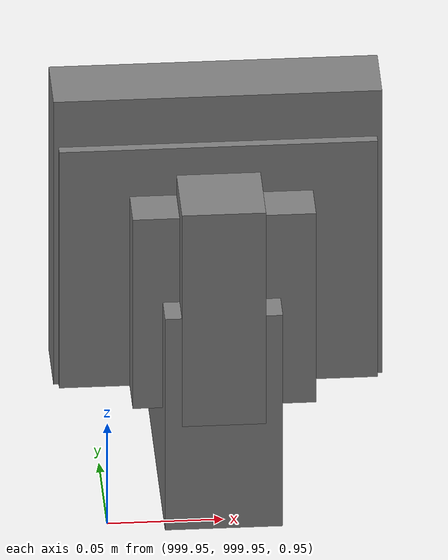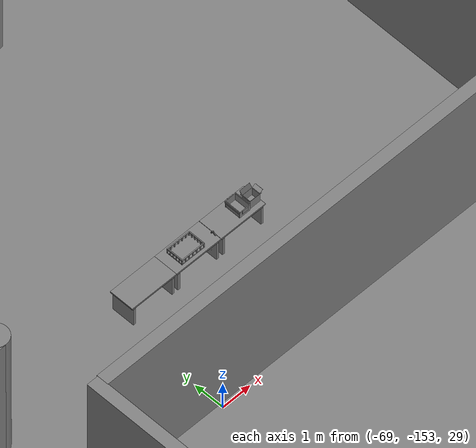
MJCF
<mujoco>
    <option gravity="0.000000000 0.000000000 -9.810000420" timestep="0.0049999999" integrator="implicitfast" density="1.225" viscosity="1.8000001e-05" noslip_iterations="10" iterations="100" sdf_iterations="50">
        <flag multiccd="disable"/>
    </option>
    <size memory="1000M"/>
    <compiler coordinate="local"/>
    <worldbody>
        <light cutoff="30" pos="0 1 1" dir="0 -1 -2"/>
        <light cutoff="30" pos="0 -1 1" dir="0 1 -2"/>
        <body pos="1000.000000000 1000.000000000 1.000000000" euler="0.000000000 0.000000000 180.000000000" name="openloong_gripper_2f85_fix_base_usda_wifi_box">
            <geom contype="1" conaffinity="1" density="1000" type="box" material="" rgba="0.500000000 0.500000000 0.500000000 1.000000000" solimp="0.899999976 0.949999988 0.001000000" friction="1.000000000 0.005000000 0.000100000" solref="0.020000000 1.000000000" margin="0" condim="3" group="0" pos="0.000000000 0.000000000 0.058978677" quat="0.000000000 0.000000047 0.000000000 1.000000000" size="0.068499997 0.018999999 0.059000000" name="openloong_gripper_2f85_fix_base_usda_geom_535E38D2_6C66_4A6D_9E98_32AD51DC69A3"/>
            <freejoint name="openloong_gripper_2f85_fix_base_usda_wifi_box_joint"/>
            <site size="0.005000000 0.005000000 0.005000000" rgba="0.500000000 0.500000000 0.500000000 1.000000000" pos="0.000000000 0.000000000 0.000000000" quat="0.999961913 0.008726500 0.000000000 0.000000000" group="0" type="sphere" name="openloong_gripper_2f85_fix_base_usda_wifi_boxsite"/>
        </body>
        <body pos="1000.000000000 1000.000000000 1.000000000" euler="0.000000000 0.000000000 180.000000000" name="openloong_gripper_2f85_fix_base_usda_battery_01">
            <geom contype="1" conaffinity="1" density="1000" type="box" material="" rgba="0.500000000 0.500000000 0.500000000 1.000000000" solimp="0.899999976 0.949999988 0.001000000" friction="1.000000000 0.005000000 0.000100000" solref="0.020000000 1.000000000" margin="0" condim="3" group="0" pos="-0.011123657 -0.041940309 0.101691343" quat="1.000000000 0.000000000 0.000000000 0.000000000" size="0.010800000 0.003375000 0.004725000" name="openloong_gripper_2f85_fix_base_usda_geom_2A04CA50_837C_4619_9FBC_A22FE351C2E5"/>
            <geom contype="1" conaffinity="1" density="1000" type="box" material="" rgba="0.500000000 0.500000000 0.500000000 1.000000000" solimp="0.899999976 0.949999988 0.001000000" friction="1.000000000 0.005000000 0.000100000" solref="0.020000000 1.000000000" margin="0" condim="3" group="0" pos="-0.010876465 -0.044247437 0.047066893" quat="0.998702705 -0.050920475 0.000000000 0.000000000" size="0.009450001 0.002700000 0.024975000" name="openloong_gripper_2f85_fix_base_usda_geom_AA7B56A0_633D_4D46_BB33_0039E451D196"/>
            <geom contype="1" conaffinity="1" density="1000" type="box" material="" rgba="0.500000000 0.500000000 0.500000000 1.000000000" solimp="0.899999976 0.949999988 0.001000000" friction="1.000000000 0.005000000 0.000100000" solref="0.020000000 1.000000000" margin="0" condim="3" group="0" pos="-0.001235962 -0.000659180 0.047381196" quat="1.000000000 0.000000000 0.000000000 0.000000000" size="0.039420001 0.039150000 0.047250003" name="openloong_gripper_2f85_fix_base_usda_geom_812FBEF0_0C6D_4E7F_87A1_90F26704485B"/>
            <geom contype="1" conaffinity="1" density="1000" type="box" material="" rgba="0.500000000 0.500000000 0.500000000 1.000000000" solimp="0.899999976 0.949999988 0.001000000" friction="1.000000000 0.005000000 0.000100000" solref="0.020000000 1.000000000" margin="0" condim="3" group="0" pos="-0.010876465 -0.039138794 0.009851727" quat="1.000000000 0.000000000 0.000000000 0.000000000" size="0.009450001 0.010800000 0.013500000" name="openloong_gripper_2f85_fix_base_usda_geom_03B27D96_58A0_4780_85FE_1F64C6559A0B"/>
            <geom contype="1" conaffinity="1" density="1000" type="box" material="" rgba="0.500000000 0.500000000 0.500000000 1.000000000" solimp="0.899999976 0.949999988 0.001000000" friction="1.000000000 0.005000000 0.000100000" solref="0.020000000 1.000000000" margin="0" condim="3" group="0" pos="-0.010876465 -0.041528322 0.071508206" quat="1.000000000 0.000000000 0.000000000 0.000000000" size="0.009450001 0.002700000 0.027000001" name="openloong_gripper_2f85_fix_base_usda_geom_D7F7D3C3_1AC4_4B35_808D_F0DFDC3CFDB6"/>
            <freejoint name="openloong_gripper_2f85_fix_base_usda_battery_01_joint"/>
            <site size="0.005000000 0.005000000 0.005000000" rgba="0.500000000 0.500000000 0.500000000 1.000000000" pos="0.000000000 0.000000000 0.000000000" quat="0.999961913 0.008726500 0.000000000 0.000000000" group="0" type="sphere" name="openloong_gripper_2f85_fix_base_usda_battery_01site"/>
        </body>
        <body pos="-66.016090393 -149.308532715 31.166820526" euler="-0.553020239 19.595533371 -167.028823853" mocap="true" name="spotlight3_SpotLight"/>
        <body pos="1000.000000000 1000.000000000 1.000000000" euler="0.000000000 0.000000000 180.000000000" name="openloong_gripper_2f85_fix_base_usda_cpu_fan">
            <geom contype="1" conaffinity="1" density="1000" type="box" material="" rgba="0.500000000 0.500000000 0.500000000 1.000000000" solimp="0.899999976 0.949999988 0.001000000" friction="1.000000000 0.005000000 0.000100000" solref="0.020000000 1.000000000" margin="0" condim="3" group="0" pos="0.000000000 0.000000000 0.070034981" quat="0.000000000 0.000000000 0.000000000 1.000000000" size="0.070700005 0.014699999 0.070700005" name="openloong_gripper_2f85_fix_base_usda_geom_D2241F4B_41E7_4568_B958_433361CD665E"/>
            <freejoint name="openloong_gripper_2f85_fix_base_usda_cpu_fan_joint"/>
            <site size="0.005000000 0.005000000 0.005000000" rgba="0.500000000 0.500000000 0.500000000 1.000000000" pos="0.000000000 0.000000000 0.000000000" quat="0.999961913 0.008726535 0.000000000 0.000000000" group="0" type="sphere" name="openloong_gripper_2f85_fix_base_usda_cpu_fancsite"/>
        </body>
        <body pos="1000.000000000 1000.000000000 1.000000000" euler="0.000011953 0.000005123 -179.999984741" name="openloong_gripper_2f85_fix_base_usda_intel_box">
            <geom contype="1" conaffinity="1" density="1000" type="box" material="" rgba="0.500000000 0.500000000 0.500000000 1.000000000" solimp="0.899999976 0.949999988 0.001000000" friction="1.000000000 0.005000000 0.000100000" solref="0.020000000 1.000000000" margin="0" condim="3" group="0" pos="0.000000000 -0.000067139 0.000082284" quat="0.707106709 0.000000225 0.000000253 0.707106650" size="0.052800003 0.025300000 0.052800003" name="openloong_gripper_2f85_fix_base_usda_geom_44325758_4702_4469_9F70_33CB09F5D6CF"/>
            <freejoint name="openloong_gripper_2f85_fix_base_usda_intel_box_joint"/>
            <site size="0.005000000 0.005000000 0.005000000" rgba="0.500000000 0.500000000 0.500000000 1.000000000" pos="0.000000000 0.000000000 0.000000000" quat="0.999961913 0.008726500 0.000000000 0.000000000" group="0" type="sphere" name="openloong_gripper_2f85_fix_base_usda_intel_boxsite"/>
        </body>
        <body pos="1000.000000000 999.999938965 1.000000000" euler="0.000000000 0.000000000 180.000000000" name="openloong_gripper_2f85_fix_base_usda_intelcore_i5">
            <geom contype="1" conaffinity="1" density="1000" type="box" material="" rgba="0.500000000 0.500000000 0.500000000 1.000000000" solimp="0.899999976 0.949999988 0.001000000" friction="1.000000000 0.005000000 0.000100000" solref="0.020000000 1.000000000" margin="0" condim="3" group="0" pos="0.000000000 0.000000000 0.051722717" quat="0.707106709 0.000000000 0.000000000 -0.707106769" size="0.052800000 0.018080002 0.052800000" name="openloong_gripper_2f85_fix_base_usda_geom_CD97EAEC_F53F_42B4_9928_0914275BCD4C"/>
            <freejoint name="openloong_gripper_2f85_fix_base_usda_intelcore_i5_joint"/>
            <site size="0.005000000 0.005000000 0.005000000" rgba="0.500000000 0.500000000 0.500000000 1.000000000" pos="0.000000000 0.000000000 0.000000000" quat="0.999961913 0.008726534 0.000000000 0.000000000" group="0" type="sphere" name="openloong_gripper_2f85_fix_base_usda_intelcore_i5site"/>
        </body>
        <body pos="-66.032958984 -149.114318848 31.170312881" euler="110.102882385 66.696701050 -165.041503906" mocap="true" name="spotlight2_SpotLight"/>
        <body pos="-66.172134399 -149.775054932 31.170455933" euler="66.334274292 72.379234314 -36.618595123" mocap="true" name="spotlight4_SpotLight"/>
        <body pos="-64.866622925 -149.383972168 30.183746338" euler="89.999984741 89.999946594 0.000000000" name="openloong_gripper_2f85_fix_base_usda_bluebox_01">
            <geom contype="1" conaffinity="1" density="1000" type="box" material="" rgba="0.500000000 0.500000000 0.500000000 1.000000000" solimp="0.899999976 0.949999988 0.001000000" friction="1.000000000 0.005000000 0.000100000" solref="0.020000000 1.000000000" margin="0" condim="3" group="0" pos="0.276580811 0.187225342 0.000068665" quat="0.707106948 0.000077471 0.707106352 0.000077486" size="0.100000001 0.057999998 0.010000000" name="openloong_gripper_2f85_fix_base_usda_geom_7D5F3761_BE4D_4C3B_8D41_05D0383416BF"/>
            <geom contype="1" conaffinity="1" density="1000" type="box" material="" rgba="0.500000000 0.500000000 0.500000000 1.000000000" solimp="0.899999976 0.949999988 0.001000000" friction="1.000000000 0.005000000 0.000100000" solref="0.020000000 1.000000000" margin="0" condim="3" group="0" pos="0.000000000 0.002883911 0.000000000" quat="0.999999881 0.000000000 0.000000000 0.000000000" size="0.254000008 0.003000000 0.172000006" name="openloong_gripper_2f85_fix_base_usda_geom_9A4B85C0_B813_4B4D_BF58_5A7FE22EA36D"/>
            <geom contype="1" conaffinity="1" density="1000" type="box" material="" rgba="0.500000000 0.500000000 0.500000000 1.000000000" solimp="0.899999976 0.949999988 0.001000000" friction="1.000000000 0.005000000 0.000100000" solref="0.020000000 1.000000000" margin="0" condim="3" group="0" pos="0.000000000 0.124874115 0.173484802" quat="0.999796331 0.020176515 -0.000000015 0.000000030" size="0.259999990 0.119999997 0.007000000" name="openloong_gripper_2f85_fix_base_usda_geom_FCF989BE_7101_4FB3_BF06_E0173B4EBD48"/>
            <geom contype="1" conaffinity="1" density="1000" type="box" material="" rgba="0.500000000 0.500000000 0.500000000 1.000000000" solimp="0.899999976 0.949999988 0.001000000" friction="1.000000000 0.005000000 0.000100000" solref="0.020000000 1.000000000" margin="0" condim="3" group="0" pos="0.000000000 0.124874115 -0.173469543" quat="0.999796331 -0.020176545 -0.000000015 0.000000000" size="0.259999990 0.119999997 0.007000000" name="openloong_gripper_2f85_fix_base_usda_geom_74E068C0_F14C_480D_8E4A_F9EAFBEF161C"/>
            <geom contype="1" conaffinity="1" density="1000" type="box" material="" rgba="0.500000000 0.500000000 0.500000000 1.000000000" solimp="0.899999976 0.949999988 0.001000000" friction="1.000000000 0.005000000 0.000100000" solref="0.020000000 1.000000000" margin="0" condim="3" group="0" pos="0.000000000 0.214008331 0.188980103" quat="0.999912977 0.013176724 0.000000015 0.000000000" size="0.259999990 0.029999999 0.012500000" name="openloong_gripper_2f85_fix_base_usda_geom_ECC2DB4D_8212_47AD_A0E6_77E61BEBB356"/>
            <geom contype="1" conaffinity="1" density="1000" type="box" material="" rgba="0.500000000 0.500000000 0.500000000 1.000000000" solimp="0.899999976 0.949999988 0.001000000" friction="1.000000000 0.005000000 0.000100000" solref="0.020000000 1.000000000" margin="0" condim="3" group="0" pos="-0.258361816 0.125289917 0.001876831" quat="0.702796936 -0.020792112 0.710783124 0.020769298" size="0.189999998 0.119999997 0.009000000" name="openloong_gripper_2f85_fix_base_usda_geom_78B0087F_3C7B_4F91_883A_7221951839E5"/>
            <geom contype="1" conaffinity="1" density="1000" type="box" material="" rgba="0.500000000 0.500000000 0.500000000 1.000000000" solimp="0.899999976 0.949999988 0.001000000" friction="1.000000000 0.005000000 0.000100000" solref="0.020000000 1.000000000" margin="0" condim="3" group="0" pos="0.000000000 0.214008331 -0.188980103" quat="0.999912977 -0.013176769 0.000000030 0.000000015" size="0.259999990 0.029999999 0.012500000" name="openloong_gripper_2f85_fix_base_usda_geom_40A17422_5417_4C55_B836_8245642DF6AF"/>
            <geom contype="1" conaffinity="1" density="1000" type="box" material="" rgba="0.500000000 0.500000000 0.500000000 1.000000000" solimp="0.899999976 0.949999988 0.001000000" friction="1.000000000 0.005000000 0.000100000" solref="0.020000000 1.000000000" margin="0" condim="3" group="0" pos="-0.276611328 0.187225342 0.000068665" quat="0.707106650 0.000077441 0.707106709 0.000077456" size="0.100000001 0.057999998 0.010000000" name="openloong_gripper_2f85_fix_base_usda_geom_7B25C0A6_04E3_4653_B9CD_F380D363F36F"/>
            <geom contype="1" conaffinity="1" density="1000" type="box" material="" rgba="0.500000000 0.500000000 0.500000000 1.000000000" solimp="0.899999976 0.949999988 0.001000000" friction="1.000000000 0.005000000 0.000100000" solref="0.020000000 1.000000000" margin="0" condim="3" group="0" pos="0.258331299 0.125289917 0.001876831" quat="0.702851415 0.018856421 0.710823774 -0.019329369" size="0.189999998 0.119999997 0.009000000" name="openloong_gripper_2f85_fix_base_usda_geom_EE455652_C96A_40BB_8978_CC87EE34F8AE"/>
            <freejoint name="openloong_gripper_2f85_fix_base_usda_bluebox_01_joint"/>
            <site size="0.005000000 0.005000000 0.005000000" rgba="0.500000000 0.500000000 0.500000000 1.000000000" pos="0.000000000 0.000000000 0.000000000" quat="0.999961913 0.008726534 0.000000000 0.000000000" group="0" type="sphere" name="openloong_gripper_2f85_fix_base_usda_bluebox_01site"/>
        </body>
        <body pos="-64.496299744 -149.491867065 30.235729218" euler="0.000000000 0.000000000 89.999946594" name="openloong_gripper_2f85_fix_base_usda_cardboardbox_01">
            <geom contype="1" conaffinity="1" density="1000" type="box" material="" rgba="0.500000000 0.500000000 0.500000000 1.000000000" solimp="0.899999976 0.949999988 0.001000000" friction="1.000000000 0.005000000 0.000100000" solref="0.020000000 1.000000000" margin="0" condim="3" group="0" pos="-0.003166199 -0.004086494 0.005052090" quat="1.000000000 0.000000000 0.000000000 0.000000000" size="0.142499998 0.177500010 0.005000000" name="openloong_gripper_2f85_fix_base_usda_geom_E5F159E0_6368_40D0_A8A7_9DF6588862CE"/>
            <geom contype="1" conaffinity="1" density="1000" type="box" material="" rgba="0.500000000 0.500000000 0.500000000 1.000000000" solimp="0.899999976 0.949999988 0.001000000" friction="1.000000000 0.005000000 0.000100000" solref="0.020000000 1.000000000" margin="0" condim="3" group="0" pos="-0.003166199 0.170316696 0.150570869" quat="1.000000000 0.000000000 0.000000000 0.000000000" size="0.142499998 0.005000000 0.149999991" name="openloong_gripper_2f85_fix_base_usda_geom_9998F2BA_2649_4DEC_BE32_4B7B55AAE383"/>
            <geom contype="1" conaffinity="1" density="1000" type="box" material="" rgba="0.500000000 0.500000000 0.500000000 1.000000000" solimp="0.899999976 0.949999988 0.001000000" friction="1.000000000 0.005000000 0.000100000" solref="0.020000000 1.000000000" margin="0" condim="3" group="0" pos="-0.147399902 -0.005307198 0.150570869" quat="1.000000000 0.000000000 0.000000000 0.000000000" size="0.005000000 0.177500010 0.149999991" name="openloong_gripper_2f85_fix_base_usda_geom_22EA0EAE_E950_4917_B234_F9FFC8CDB180"/>
            <geom contype="1" conaffinity="1" density="1000" type="box" material="" rgba="0.500000000 0.500000000 0.500000000 1.000000000" solimp="0.899999976 0.949999988 0.001000000" friction="1.000000000 0.005000000 0.000100000" solref="0.020000000 1.000000000" margin="0" condim="3" group="0" pos="0.140275955 -0.005307198 0.150570869" quat="1.000000000 0.000000000 0.000000000 0.000000000" size="0.005000000 0.177500010 0.149999991" name="openloong_gripper_2f85_fix_base_usda_geom_DB9910E1_B250_409B_939B_A88C914817A6"/>
            <geom contype="1" conaffinity="1" density="1000" type="box" material="" rgba="0.500000000 0.500000000 0.500000000 1.000000000" solimp="0.899999976 0.949999988 0.001000000" friction="1.000000000 0.005000000 0.000100000" solref="0.020000000 1.000000000" margin="0" condim="3" group="0" pos="-0.003166199 -0.181550980 0.150570869" quat="1.000000000 0.000000000 0.000000000 0.000000000" size="0.142499998 0.005000000 0.149999991" name="openloong_gripper_2f85_fix_base_usda_geom_86E58D52_B5E6_4F9B_8616_E8237EAA258E"/>
            <freejoint name="openloong_gripper_2f85_fix_base_usda_cardboardbox_01_joint"/>
            <site size="0.005000000 0.005000000 0.005000000" rgba="0.500000000 0.500000000 0.500000000 1.000000000" pos="0.000000000 0.000000000 0.000000000" quat="0.999961913 0.008726535 0.000000000 0.000000000" group="0" type="sphere" name="openloong_gripper_2f85_fix_base_usda_site_E16346E0_5366_4F3B_9B90_5BAC51886AA6"/>
            <body pos="0.139160156 -0.004048347 0.301930904" euler="-179.999954224 49.383502960 179.999954224" name="openloong_gripper_2f85_fix_base_usda_A1_006">
                <geom contype="1" conaffinity="1" density="1000" type="box" material="" rgba="0.500000000 0.500000000 0.500000000 1.000000000" solimp="0.899999976 0.949999988 0.001000000" friction="1.000000000 0.005000000 0.000100000" solref="0.020000000 1.000000000" margin="0" condim="3" group="0" pos="-0.071587563 0.000009537 0.001745224" quat="0.999999881 0.000000000 0.000000000 0.000000000" size="0.071249999 0.179999992 0.002500000" name="openloong_gripper_2f85_fix_base_usda_geom_8C4E95CB_B592_4A1B_9750_BBF580073106"/>
                <joint armature="0" stiffness="0.07" damping="0.0099999998" axis="0.000000 1.000000 0.000000" type="hinge" name="openloong_gripper_2f85_fix_base_usda_A1_006"/>
            </body>
            <body pos="-0.145902634 -0.004086494 0.301938057" euler="-180.000000000 -60.000011444 -180.000000000" name="openloong_gripper_2f85_fix_base_usda_A2_006">
                <geom contype="1" conaffinity="1" density="1000" type="box" material="" rgba="0.500000000 0.500000000 0.500000000 1.000000000" solimp="0.899999976 0.949999988 0.001000000" friction="1.000000000 0.005000000 0.000100000" solref="0.020000000 1.000000000" margin="0" condim="3" group="0" pos="0.071268082 0.000009537 0.002717972" quat="0.000002921 0.000000000 -0.000000030 0.999999881" size="0.071249999 0.179999992 0.002500000" name="openloong_gripper_2f85_fix_base_usda_geom_A62F5C92_5C91_4AAD_A371_1AF331FDF035"/>
                <joint armature="0" stiffness="0.07" damping="0.0099999998" axis="0.000000 1.000000 0.000000" type="hinge" name="openloong_gripper_2f85_fix_base_usda_A2_006"/>
            </body>
            <body pos="-0.003385544 0.175991058 0.301930904" euler="-125.858116150 -0.000004561 0.000002331" name="openloong_gripper_2f85_fix_base_usda_B2_006">
                <geom contype="1" conaffinity="1" density="1000" type="box" material="" rgba="0.500000000 0.500000000 0.500000000 1.000000000" solimp="0.899999976 0.949999988 0.001000000" friction="1.000000000 0.005000000 0.000100000" solref="0.020000000 1.000000000" margin="0" condim="3" group="0" pos="0.000009537 -0.070939064 -0.002470016" quat="0.999614120 0.027776197 -0.000000015 0.000000030" size="0.137500003 0.064999998 0.005000000" name="openloong_gripper_2f85_fix_base_usda_geom_5438A7C1_9406_4E89_B8B3_FBC6C3AA0397"/>
                <joint armature="0" stiffness="0.07" damping="0.0099999998" axis="1.000000 0.000000 0.000000" type="hinge" name="openloong_gripper_2f85_fix_base_usda_B2_006"/>
            </body>
            <body pos="-0.003385544 -0.184140205 0.301938057" euler="147.805557251 0.000000000 0.000000000" name="openloong_gripper_2f85_fix_base_usda_B1_006">
                <geom contype="1" conaffinity="1" density="1000" type="box" material="" rgba="0.500000000 0.500000000 0.500000000 1.000000000" solimp="0.899999976 0.949999988 0.001000000" friction="1.000000000 0.005000000 0.000100000" solref="0.020000000 1.000000000" margin="0" condim="3" group="0" pos="-0.000028610 0.070202351 -0.002703667" quat="0.999614179 -0.027776167 0.000000000 0.000000000" size="0.137500003 0.064999998 0.005000000" name="openloong_gripper_2f85_fix_base_usda_geom_8B3C5501_141F_436E_82D9_6ADABA1EE4A9"/>
                <joint armature="0" stiffness="0.07" damping="0.0099999998" axis="1.000000 0.000000 0.000000" type="hinge" name="openloong_gripper_2f85_fix_base_usda_B1_006"/>
            </body>
        </body>
        <body pos="-65.882858276 -149.481979370 30.229999542" euler="-64.487716675 0.000000000 0.000000000" name="openloong_gripper_2f85_fix_base_usda_Barcode">
            <geom contype="1" conaffinity="1" density="1000" type="box" material="" rgba="0.500000000 0.500000000 0.500000000 1.000000000" solimp="0.899999976 0.949999988 0.001000000" friction="1.000000000 0.005000000 0.000100000" solref="0.020000000 1.000000000" margin="0" condim="3" group="0" pos="0.000000000 0.013038635 0.001419067" quat="0.000000000 0.000000000 0.000000000 1.000000119" size="0.034000002 0.010000000 0.017999999" name="openloong_gripper_2f85_fix_base_usda_geom_6C62F95D_A59A_4A12_8A0E_329D2930133B"/>
            <geom contype="1" conaffinity="1" density="1000" type="box" material="" rgba="0.500000000 0.500000000 0.500000000 1.000000000" solimp="0.899999976 0.949999988 0.001000000" friction="1.000000000 0.005000000 0.000100000" solref="0.020000000 1.000000000" margin="0" condim="3" group="0" pos="0.000000000 -0.035301208 -0.007095337" quat="0.000000000 0.000000000 -0.043619365 0.999048233" size="0.028999999 0.010000000 0.020000000" name="openloong_gripper_2f85_fix_base_usda_geom_0E884782_AC88_498E_94B5_5901D7BA9F4D"/>
            <geom contype="1" conaffinity="1" density="1000" type="box" material="" rgba="0.500000000 0.500000000 0.500000000 1.000000000" solimp="0.899999976 0.949999988 0.001000000" friction="1.000000000 0.005000000 0.000100000" solref="0.020000000 1.000000000" margin="0" condim="3" group="0" pos="0.000000000 -0.043411255 -0.011749268" quat="0.922262907 0.386563420 0.000000000 0.000000000" size="0.026000001 0.010000000 0.020000000" name="openloong_gripper_2f85_fix_base_usda_geom_B6EB6266_69A1_48B8_9EF5_675024B232F5"/>
            <geom contype="1" conaffinity="1" density="1000" type="box" material="" rgba="0.500000000 0.500000000 0.500000000 1.000000000" solimp="0.899999976 0.949999988 0.001000000" friction="1.000000000 0.005000000 0.000100000" solref="0.020000000 1.000000000" margin="0" condim="3" group="0" pos="0.000000000 -0.016967773 -0.031860352" quat="0.000000000 0.000000000 0.000000000 1.000000119" size="0.008000000 0.010000000 0.013000000" name="openloong_gripper_2f85_fix_base_usda_geom_06C2CA1F_E0AD_4715_AFB8_AB686C95EC95"/>
            <geom contype="1" conaffinity="1" density="1000" type="box" material="" rgba="0.500000000 0.500000000 0.500000000 1.000000000" solimp="0.899999976 0.949999988 0.001000000" friction="1.000000000 0.005000000 0.000100000" solref="0.020000000 1.000000000" margin="0" condim="3" group="0" pos="0.000000000 -0.001869202 0.000312805" quat="0.953716993 0.300705761 0.000000000 0.000000000" size="0.032000002 0.010000000 0.018999999" name="openloong_gripper_2f85_fix_base_usda_geom_69A9B651_129D_4921_B8E6_7C025688038B"/>
            <geom contype="1" conaffinity="1" density="1000" type="box" material="" rgba="0.500000000 0.500000000 0.500000000 1.000000000" solimp="0.899999976 0.949999988 0.001000000" friction="1.000000000 0.005000000 0.000100000" solref="0.020000000 1.000000000" margin="0" condim="3" group="0" pos="0.000000000 -0.019531250 -0.003173828" quat="0.953716993 0.300705761 0.000000000 0.000000000" size="0.030999999 0.010000000 0.020000000" name="openloong_gripper_2f85_fix_base_usda_geom_A9FC6FFF_B7FE_420A_B036_AC3B084D390F"/>
            <geom contype="1" conaffinity="1" density="1000" type="box" material="" rgba="0.500000000 0.500000000 0.500000000 1.000000000" solimp="0.899999976 0.949999988 0.001000000" friction="1.000000000 0.005000000 0.000100000" solref="0.020000000 1.000000000" margin="0" condim="3" group="0" pos="0.000000000 -0.035301208 -0.007095337" quat="0.953716993 0.300705761 0.000000000 0.000000000" size="0.028999999 0.010000000 0.020000000" name="openloong_gripper_2f85_fix_base_usda_geom_6416DFE5_BD5B_4BD8_8611_0357CEE21B14"/>
            <geom contype="1" conaffinity="1" density="1000" type="box" material="" rgba="0.500000000 0.500000000 0.500000000 1.000000000" solimp="0.899999976 0.949999988 0.001000000" friction="1.000000000 0.005000000 0.000100000" solref="0.020000000 1.000000000" margin="0" condim="3" group="0" pos="0.000000000 -0.042617798 -0.071121216" quat="0.000000000 0.000000000 0.000000000 1.000000119" size="0.013000000 0.021000000 0.059999999" name="openloong_gripper_2f85_fix_base_usda_geom_2A21316C_2F4D_4356_A5CF_6B2562F0A6E3"/>
            <freejoint name="openloong_gripper_2f85_fix_base_usda_Barcode_joint"/>
            <site size="0.005000000 0.005000000 0.005000000" rgba="0.500000000 0.500000000 0.500000000 1.000000000" pos="0.000000000 0.000000000 0.000000000" quat="1.000000000 0.000000000 0.000000000 0.000000000" group="0" type="sphere" name="openloong_gripper_2f85_fix_base_usda_Barcode_site"/>
        </body>
        <body pos="-66.745018005 -149.392349243 30.184000015" euler="0.000000000 0.000000000 89.999946594" name="[22333812345405]_Basket_01">
            <geom contype="1" conaffinity="1" density="1000" type="box" material="" rgba="0.500000000 0.500000000 0.500000000 1.000000000" solimp="0.899999976 0.949999988 0.001000000" friction="1.000000000 0.005000000 0.000100000" solref="0.020000000 1.000000000" margin="0" condim="3" group="0" pos="-0.052425385 0.389207840 0.089787483" quat="0.707107008 0.000000000 0.000000000 0.707106411" size="0.014249999 0.014249999 0.059999999" name="[22333812345405]_geom_2E384759_51E7_4053_9E14_ED6A6D0DC106"/>
            <geom contype="1" conaffinity="1" density="1000" type="box" material="" rgba="0.500000000 0.500000000 0.500000000 1.000000000" solimp="0.899999976 0.949999988 0.001000000" friction="1.000000000 0.005000000 0.000100000" solref="0.020000000 1.000000000" margin="0" condim="3" group="0" pos="0.264015198 -0.133043289 0.089787483" quat="0.707107008 0.000000000 0.000000000 0.707106411" size="0.014249999 0.014249999 0.059999999" name="[22333812345405]_geom_742FF534_C7D1_4B6E_A7A1_EF33641EB4F0"/>
            <geom contype="1" conaffinity="1" density="1000" type="box" material="" rgba="0.500000000 0.500000000 0.500000000 1.000000000" solimp="0.899999976 0.949999988 0.001000000" friction="1.000000000 0.005000000 0.000100000" solref="0.020000000 1.000000000" margin="0" condim="3" group="0" pos="-0.264015198 -0.265548706 0.089793205" quat="0.707107008 0.000000000 0.000000000 0.707106411" size="0.014249999 0.014249999 0.059999999" name="[22333812345405]_geom_C2F2F405_1AFE_44C9_A2B7_ACC6393666FB"/>
            <geom contype="1" conaffinity="1" density="1000" type="box" material="" rgba="0.500000000 0.500000000 0.500000000 1.000000000" solimp="0.899999976 0.949999988 0.001000000" friction="1.000000000 0.005000000 0.000100000" solref="0.020000000 1.000000000" margin="0" condim="3" group="0" pos="-0.160263062 -0.389322281 0.089793205" quat="0.707107008 0.000000000 0.000000000 0.707106411" size="0.014249999 0.014249999 0.059999999" name="[22333812345405]_geom_4BEE1413_E964_44DB_8507_B6FA8148E6A7"/>
            <geom contype="1" conaffinity="1" density="1000" type="box" material="" rgba="0.500000000 0.500000000 0.500000000 1.000000000" solimp="0.899999976 0.949999988 0.001000000" friction="1.000000000 0.005000000 0.000100000" solref="0.020000000 1.000000000" margin="0" condim="3" group="0" pos="0.162265778 -0.389322281 0.089787483" quat="0.707107008 0.000000000 0.000000000 0.707106411" size="0.014249999 0.014249999 0.059999999" name="[22333812345405]_geom_A09421A5_96AE_4DF6_A155_79C7A00D280E"/>
            <geom contype="1" conaffinity="1" density="1000" type="box" material="" rgba="0.500000000 0.500000000 0.500000000 1.000000000" solimp="0.899999976 0.949999988 0.001000000" friction="1.000000000 0.005000000 0.000100000" solref="0.020000000 1.000000000" margin="0" condim="3" group="0" pos="0.264015198 0.389207840 0.089787483" quat="0.707107008 0.000000000 0.000000000 0.707106411" size="0.014249999 0.014249999 0.059999999" name="[22333812345405]_geom_B38BDD21_7F9B_42D2_A873_006E9B75CA9A"/>
            <geom contype="1" conaffinity="1" density="1000" type="box" material="" rgba="0.500000000 0.500000000 0.500000000 1.000000000" solimp="0.899999976 0.949999988 0.001000000" friction="1.000000000 0.005000000 0.000100000" solref="0.020000000 1.000000000" margin="0" condim="3" group="0" pos="-0.264015198 -0.133043289 0.089793205" quat="0.707107008 0.000000000 0.000000000 0.707106411" size="0.014249999 0.014249999 0.059999999" name="[22333812345405]_geom_DD29FFDA_CCC8_4B66_986A_A8EC7AFDAA7C"/>
            <geom contype="1" conaffinity="1" density="1000" type="box" material="" rgba="0.500000000 0.500000000 0.500000000 1.000000000" solimp="0.899999976 0.949999988 0.001000000" friction="1.000000000 0.005000000 0.000100000" solref="0.020000000 1.000000000" margin="0" condim="3" group="0" pos="-0.264026642 0.269256592 0.089793205" quat="0.707107008 0.000000000 0.000000000 0.707106411" size="0.014249999 0.014249999 0.059999999" name="[22333812345405]_geom_C292C5DC_4574_47FE_9A23_DD538B32974C"/>
            <geom contype="1" conaffinity="1" density="1000" type="box" material="" rgba="0.500000000 0.500000000 0.500000000 1.000000000" solimp="0.899999976 0.949999988 0.001000000" friction="1.000000000 0.005000000 0.000100000" solref="0.020000000 1.000000000" margin="0" condim="3" group="0" pos="0.054462433 0.389207840 0.089787483" quat="0.707107008 0.000000000 0.000000000 0.707106411" size="0.014249999 0.014249999 0.059999999" name="[22333812345405]_geom_04DEA1D1_CECC_4F48_AF9A_4EFFC2B66C52"/>
            <geom contype="1" conaffinity="1" density="1000" type="box" material="" rgba="0.500000000 0.500000000 0.500000000 1.000000000" solimp="0.899999976 0.949999988 0.001000000" friction="1.000000000 0.005000000 0.000100000" solref="0.020000000 1.000000000" margin="0" condim="3" group="0" pos="0.054462433 -0.389322281 0.089787483" quat="0.707107008 0.000000000 0.000000000 0.707106411" size="0.014249999 0.014249999 0.059999999" name="[22333812345405]_geom_671DCCAA_EA28_454C_BD92_2DEEC2456A06"/>
            <geom contype="1" conaffinity="1" density="1000" type="box" material="" rgba="0.500000000 0.500000000 0.500000000 1.000000000" solimp="0.899999976 0.949999988 0.001000000" friction="1.000000000 0.005000000 0.000100000" solref="0.020000000 1.000000000" margin="0" condim="3" group="0" pos="0.264015198 0.269256592 0.089793205" quat="0.707107008 0.000000000 0.000000000 0.707106411" size="0.014249999 0.014249999 0.059999999" name="[22333812345405]_geom_1EEDB3BB_7F23_42E3_802A_D5D309323855"/>
            <geom contype="1" conaffinity="1" density="1000" type="box" material="" rgba="0.500000000 0.500000000 0.500000000 1.000000000" solimp="0.899999976 0.949999988 0.001000000" friction="1.000000000 0.005000000 0.000100000" solref="0.020000000 1.000000000" margin="0" condim="3" group="0" pos="0.264015198 -0.389322281 0.089787483" quat="0.707107008 0.000000000 0.000000000 0.707106411" size="0.014249999 0.014249999 0.059999999" name="[22333812345405]_geom_D572CF19_D625_4F56_8C59_D81F574E1921"/>
            <geom contype="1" conaffinity="1" density="1000" type="box" material="" rgba="0.500000000 0.500000000 0.500000000 1.000000000" solimp="0.899999976 0.949999988 0.001000000" friction="1.000000000 0.005000000 0.000100000" solref="0.020000000 1.000000000" margin="0" condim="3" group="0" pos="0.000000000 0.000000000 0.015998840" quat="0.707107008 0.000000000 0.000000000 0.707106411" size="0.403499991 0.279000014 0.015750000" name="[22333812345405]_geom_BC5132C1_8492_4B4F_83F1_1CBC27E5E245"/>
            <geom contype="1" conaffinity="1" density="1000" type="box" material="" rgba="0.500000000 0.500000000 0.500000000 1.000000000" solimp="0.899999976 0.949999988 0.001000000" friction="1.000000000 0.005000000 0.000100000" solref="0.020000000 1.000000000" margin="0" condim="3" group="0" pos="0.000000000 -0.389476776 0.163619041" quat="0.707107008 0.000000000 0.000000000 0.707106411" size="0.015000000 0.277500004 0.015750000" name="[22333812345405]_geom_58F0DD2B_59D9_404D_9584_A12FE96A0056"/>
            <geom contype="1" conaffinity="1" density="1000" type="box" material="" rgba="0.500000000 0.500000000 0.500000000 1.000000000" solimp="0.899999976 0.949999988 0.001000000" friction="1.000000000 0.005000000 0.000100000" solref="0.020000000 1.000000000" margin="0" condim="3" group="0" pos="0.162265778 0.389207840 0.089787483" quat="0.707107008 0.000000000 0.000000000 0.707106411" size="0.014249999 0.014249999 0.059999999" name="[22333812345405]_geom_5643FF32_90A3_48EF_9B65_438E37EB953B"/>
            <geom contype="1" conaffinity="1" density="1000" type="box" material="" rgba="0.500000000 0.500000000 0.500000000 1.000000000" solimp="0.899999976 0.949999988 0.001000000" friction="1.000000000 0.005000000 0.000100000" solref="0.020000000 1.000000000" margin="0" condim="3" group="0" pos="0.000000000 0.389471054 0.163619041" quat="0.707107008 0.000000000 0.000000000 0.707106411" size="0.015000000 0.277500004 0.015750000" name="[22333812345405]_geom_28CCB090_B9FB_4831_BE91_161E2D5B0F36"/>
            <geom contype="1" conaffinity="1" density="1000" type="box" material="" rgba="0.500000000 0.500000000 0.500000000 1.000000000" solimp="0.899999976 0.949999988 0.001000000" friction="1.000000000 0.005000000 0.000100000" solref="0.020000000 1.000000000" margin="0" condim="3" group="0" pos="-0.263511658 0.000000000 0.163619041" quat="0.707107008 0.000000000 0.000000000 0.707106411" size="0.403499991 0.015000000 0.015750000" name="[22333812345405]_geom_ECC15B49_846A_40AD_A45A_FC23293426EC"/>
            <geom contype="1" conaffinity="1" density="1000" type="box" material="" rgba="0.500000000 0.500000000 0.500000000 1.000000000" solimp="0.899999976 0.949999988 0.001000000" friction="1.000000000 0.005000000 0.000100000" solref="0.020000000 1.000000000" margin="0" condim="3" group="0" pos="-0.264015198 0.141334534 0.089793205" quat="0.707107008 0.000000000 0.000000000 0.707106411" size="0.014249999 0.014249999 0.059999999" name="[22333812345405]_geom_715A9438_B1DA_48A6_BE9B_C99883397AD2"/>
            <geom contype="1" conaffinity="1" density="1000" type="box" material="" rgba="0.500000000 0.500000000 0.500000000 1.000000000" solimp="0.899999976 0.949999988 0.001000000" friction="1.000000000 0.005000000 0.000100000" solref="0.020000000 1.000000000" margin="0" condim="3" group="0" pos="0.264015198 -0.265548706 0.089787483" quat="0.707107008 0.000000000 0.000000000 0.707106411" size="0.014249999 0.014249999 0.059999999" name="[22333812345405]_geom_90539E5E_7F27_48C4_A5DE_1A561B16F6F8"/>
            <geom contype="1" conaffinity="1" density="1000" type="box" material="" rgba="0.500000000 0.500000000 0.500000000 1.000000000" solimp="0.899999976 0.949999988 0.001000000" friction="1.000000000 0.005000000 0.000100000" solref="0.020000000 1.000000000" margin="0" condim="3" group="0" pos="-0.160263062 0.389207840 0.089787483" quat="0.707107008 0.000000000 0.000000000 0.707106411" size="0.014249999 0.014249999 0.059999999" name="[22333812345405]_geom_2D8E48B9_FC30_4B3E_80FA_10389CFCA2D0"/>
            <geom contype="1" conaffinity="1" density="1000" type="box" material="" rgba="0.500000000 0.500000000 0.500000000 1.000000000" solimp="0.899999976 0.949999988 0.001000000" friction="1.000000000 0.005000000 0.000100000" solref="0.020000000 1.000000000" margin="0" condim="3" group="0" pos="-0.052425385 -0.389322281 0.089787483" quat="0.707107008 0.000000000 0.000000000 0.707106411" size="0.014249999 0.014249999 0.059999999" name="[22333812345405]_geom_2A0A2B20_EFB5_4DD1_A24A_10F343FE19AA"/>
            <geom contype="1" conaffinity="1" density="1000" type="box" material="" rgba="0.500000000 0.500000000 0.500000000 1.000000000" solimp="0.899999976 0.949999988 0.001000000" friction="1.000000000 0.005000000 0.000100000" solref="0.020000000 1.000000000" margin="0" condim="3" group="0" pos="-0.264026642 -0.389322281 0.089793205" quat="0.707107008 0.000000000 0.000000000 0.707106411" size="0.014249999 0.014249999 0.059999999" name="[22333812345405]_geom_612F4AA5_E42C_401B_96FF_7F6AB50078EE"/>
            <geom contype="1" conaffinity="1" density="1000" type="box" material="" rgba="0.500000000 0.500000000 0.500000000 1.000000000" solimp="0.899999976 0.949999988 0.001000000" friction="1.000000000 0.005000000 0.000100000" solref="0.020000000 1.000000000" margin="0" condim="3" group="0" pos="0.264015198 0.141334534 0.089787483" quat="0.707107008 0.000000000 0.000000000 0.707106411" size="0.014249999 0.014249999 0.059999999" name="[22333812345405]_geom_68AF1DF6_C814_49C9_988F_6E1331E5FD65"/>
            <geom contype="1" conaffinity="1" density="1000" type="box" material="" rgba="0.500000000 0.500000000 0.500000000 1.000000000" solimp="0.899999976 0.949999988 0.001000000" friction="1.000000000 0.005000000 0.000100000" solref="0.020000000 1.000000000" margin="0" condim="3" group="0" pos="-0.264015198 0.389207840 0.089793205" quat="0.707107008 0.000000000 0.000000000 0.707106411" size="0.014249999 0.014249999 0.059999999" name="[22333812345405]_geom_AA3448FB_FD4E_4385_8D74_3F48F8DF749F"/>
            <geom contype="1" conaffinity="1" density="1000" type="box" material="" rgba="0.500000000 0.500000000 0.500000000 1.000000000" solimp="0.899999976 0.949999988 0.001000000" friction="1.000000000 0.005000000 0.000100000" solref="0.020000000 1.000000000" margin="0" condim="3" group="0" pos="0.264015198 0.004480362 0.089787483" quat="0.707107008 0.000000000 0.000000000 0.707106411" size="0.014249999 0.014249999 0.059999999" name="[22333812345405]_geom_601C6F05_AB23_408B_AA37_95B521F0F0F2"/>
            <geom contype="1" conaffinity="1" density="1000" type="box" material="" rgba="0.500000000 0.500000000 0.500000000 1.000000000" solimp="0.899999976 0.949999988 0.001000000" friction="1.000000000 0.005000000 0.000100000" solref="0.020000000 1.000000000" margin="0" condim="3" group="0" pos="0.263694763 -0.000011444 0.163619041" quat="0.707107008 0.000000000 0.000000000 0.707106411" size="0.403499991 0.015000000 0.015750000" name="[22333812345405]_geom_0E61BAA3_792E_4C91_AA3E_E6840DC8AF80"/>
            <geom contype="1" conaffinity="1" density="1000" type="box" material="" rgba="0.500000000 0.500000000 0.500000000 1.000000000" solimp="0.899999976 0.949999988 0.001000000" friction="1.000000000 0.005000000 0.000100000" solref="0.020000000 1.000000000" margin="0" condim="3" group="0" pos="-0.264015198 0.004480362 0.089793205" quat="0.707107008 0.000000000 0.000000000 0.707106411" size="0.014249999 0.014249999 0.059999999" name="[22333812345405]_geom_5077B750_5AE6_49D7_8F74_79BB925406BE"/>
            <freejoint name="[22333812345405]_joint_3C6E1450_11AC_4F0D_A513_2E4CD3E98AA4"/>
        </body>
        <body pos="0.000000000 0.000000000 0.000000000" euler="0.000000000 0.000000000 0.000000000" name="Static Objects_Static Objects">
            <geom contype="1" conaffinity="1" density="1000" type="box" material="" rgba="0.500000000 0.500000000 0.500000000 1.000000000" solimp="0.899999976 0.949999988 0.001000000" friction="1.000000000 0.005000000 0.000100000" solref="0.020000000 1.000000000" margin="0" condim="3" group="0" pos="-67.544113159 -149.365814209 29.727830887" quat="0.500000417 0.499999970 0.499999553 0.499999970" size="0.381000012 0.319999993 0.041000001" name="Static Objects_geom_95440A2A_4FF7_4F0E_9490_1EDD4460C331"/>
            <geom contype="1" conaffinity="1" density="1000" type="box" material="" rgba="0.500000000 0.500000000 0.500000000 1.000000000" solimp="0.899999976 0.949999988 0.001000000" friction="1.000000000 0.005000000 0.000100000" solref="0.020000000 1.000000000" margin="0" condim="3" group="0" pos="-68.239501953 -149.365814209 30.086868286" quat="0.500000417 0.499999970 0.499999553 0.499999970" size="0.370999992 0.039500002 0.745000005" name="Static Objects_geom_699C1414_8D43_4737_B118_ABBA477ADCC8"/>
            <geom contype="1" conaffinity="1" density="1000" type="box" material="" rgba="0.500000000 0.500000000 0.500000000 1.000000000" solimp="0.899999976 0.949999988 0.001000000" friction="1.000000000 0.005000000 0.000100000" solref="0.020000000 1.000000000" margin="0" condim="3" group="0" pos="-68.239501953 -149.365814209 30.147235870" quat="0.500000417 0.499999970 0.499999553 0.499999970" size="0.400000006 0.022000000 0.800000012" name="Static Objects_geom_6C016997_2D10_44B9_AB9D_E635B7BC4007"/>
            <geom contype="1" conaffinity="1" density="1000" type="box" material="" rgba="0.500000000 0.500000000 0.500000000 1.000000000" solimp="0.899999976 0.949999988 0.001000000" friction="1.000000000 0.005000000 0.000100000" solref="0.020000000 1.000000000" margin="0" condim="3" group="0" pos="-68.934890747 -149.365814209 29.727830887" quat="0.500000417 0.499999970 0.499999553 0.499999970" size="0.381000012 0.319999993 0.041000001" name="Static Objects_geom_06FC1BDA_C35E_4C46_8A2B_97720144FA1E"/>
            <geom contype="1" conaffinity="1" density="1000" type="box" material="" rgba="0.500000000 0.500000000 0.500000000 1.000000000" solimp="0.899999976 0.949999988 0.001000000" friction="1.000000000 0.005000000 0.000100000" solref="0.020000000 1.000000000" margin="0" condim="3" group="0" pos="-68.239501953 -149.365814209 29.561563492" quat="0.500000417 0.499999970 0.499999553 0.499999970" size="0.020000000 0.022000000 0.660000026" name="Static Objects_geom_B6D285FF_EEB9_4750_9723_D7090C6EC2DD"/>
            <geom contype="1" conaffinity="1" density="1000" type="box" material="" rgba="0.500000000 0.500000000 0.500000000 1.000000000" solimp="0.899999976 0.949999988 0.001000000" friction="1.000000000 0.005000000 0.000100000" solref="0.020000000 1.000000000" margin="0" condim="3" group="0" pos="-65.945671082 -149.365814209 29.727830887" quat="0.500000417 0.499999970 0.499999553 0.499999970" size="0.381000012 0.319999993 0.041000001" name="Static Objects_geom_E585C7FF_C320_4088_9AA8_9DD264B18EBA"/>
            <geom contype="1" conaffinity="1" density="1000" type="box" material="" rgba="0.500000000 0.500000000 0.500000000 1.000000000" solimp="0.899999976 0.949999988 0.001000000" friction="1.000000000 0.005000000 0.000100000" solref="0.020000000 1.000000000" margin="0" condim="3" group="0" pos="-66.641059875 -149.365814209 30.086868286" quat="0.500000417 0.499999970 0.499999553 0.499999970" size="0.370999992 0.039500002 0.745000005" name="Static Objects_geom_B8C16405_CB13_431E_B5FA_CFFEE664C2E8"/>
            <geom contype="1" conaffinity="1" density="1000" type="box" material="" rgba="0.500000000 0.500000000 0.500000000 1.000000000" solimp="0.899999976 0.949999988 0.001000000" friction="1.000000000 0.005000000 0.000100000" solref="0.020000000 1.000000000" margin="0" condim="3" group="0" pos="-66.641059875 -149.365814209 30.147235870" quat="0.500000417 0.499999970 0.499999553 0.499999970" size="0.400000006 0.022000000 0.800000012" name="Static Objects_geom_637CEB8A_27D2_42F3_8877_3E14D454FA6A"/>
            <geom contype="1" conaffinity="1" density="1000" type="box" material="" rgba="0.500000000 0.500000000 0.500000000 1.000000000" solimp="0.899999976 0.949999988 0.001000000" friction="1.000000000 0.005000000 0.000100000" solref="0.020000000 1.000000000" margin="0" condim="3" group="0" pos="-67.336448669 -149.365814209 29.727830887" quat="0.500000417 0.499999970 0.499999553 0.499999970" size="0.381000012 0.319999993 0.041000001" name="Static Objects_geom_8F6A194E_6A75_4C79_9AAB_E19E58EA8C6C"/>
            <geom contype="1" conaffinity="1" density="1000" type="box" material="" rgba="0.500000000 0.500000000 0.500000000 1.000000000" solimp="0.899999976 0.949999988 0.001000000" friction="1.000000000 0.005000000 0.000100000" solref="0.020000000 1.000000000" margin="0" condim="3" group="0" pos="-66.641059875 -149.365814209 29.561563492" quat="0.500000417 0.499999970 0.499999553 0.499999970" size="0.020000000 0.022000000 0.660000026" name="Static Objects_geom_C5D97884_ADF5_4818_8434_085B7C40CA9D"/>
            <geom contype="1" conaffinity="1" density="1000" type="box" material="" rgba="0.500000000 0.500000000 0.500000000 1.000000000" solimp="0.899999976 0.949999988 0.001000000" friction="1.000000000 0.005000000 0.000100000" solref="0.020000000 1.000000000" margin="0" condim="3" group="0" pos="-64.338577271 -149.365814209 29.727830887" quat="0.500000417 0.499999970 0.499999553 0.499999970" size="0.381000012 0.319999993 0.041000001" name="Static Objects_geom_1D99D587_AD43_444C_8583_8F9D80A9C123"/>
            <geom contype="1" conaffinity="1" density="1000" type="box" material="" rgba="0.500000000 0.500000000 0.500000000 1.000000000" solimp="0.899999976 0.949999988 0.001000000" friction="1.000000000 0.005000000 0.000100000" solref="0.020000000 1.000000000" margin="0" condim="3" group="0" pos="-65.033966064 -149.365814209 30.086868286" quat="0.500000417 0.499999970 0.499999553 0.499999970" size="0.370999992 0.039500002 0.745000005" name="Static Objects_geom_8E6ACDAC_14D3_4396_ACEA_BE455BA5EB67"/>
            <geom contype="1" conaffinity="1" density="1000" type="box" material="" rgba="0.500000000 0.500000000 0.500000000 1.000000000" solimp="0.899999976 0.949999988 0.001000000" friction="1.000000000 0.005000000 0.000100000" solref="0.020000000 1.000000000" margin="0" condim="3" group="0" pos="-65.033966064 -149.365814209 30.147235870" quat="0.500000417 0.499999970 0.499999553 0.499999970" size="0.400000006 0.022000000 0.800000012" name="Static Objects_geom_2C7D2158_320F_4D2A_B5C9_C1FBE412891B"/>
            <geom contype="1" conaffinity="1" density="1000" type="box" material="" rgba="0.500000000 0.500000000 0.500000000 1.000000000" solimp="0.899999976 0.949999988 0.001000000" friction="1.000000000 0.005000000 0.000100000" solref="0.020000000 1.000000000" margin="0" condim="3" group="0" pos="-65.729354858 -149.365814209 29.727830887" quat="0.500000417 0.499999970 0.499999553 0.499999970" size="0.381000012 0.319999993 0.041000001" name="Static Objects_geom_17459248_3DAE_48C2_B50C_AC14AB27042B"/>
            <geom contype="1" conaffinity="1" density="1000" type="box" material="" rgba="0.500000000 0.500000000 0.500000000 1.000000000" solimp="0.899999976 0.949999988 0.001000000" friction="1.000000000 0.005000000 0.000100000" solref="0.020000000 1.000000000" margin="0" condim="3" group="0" pos="-65.033966064 -149.365814209 29.561563492" quat="0.500000417 0.499999970 0.499999553 0.499999970" size="0.020000000 0.022000000 0.660000026" name="Static Objects_geom_02151EB0_E28C_4912_8246_82D52B2D3A8E"/>
            <geom contype="1" conaffinity="1" density="1000" type="box" material="" rgba="0.500000000 0.500000000 0.500000000 1.000000000" solimp="0.899999976 0.949999988 0.001000000" friction="1.000000000 0.005000000 0.000100000" solref="0.020000000 1.000000000" margin="0" condim="3" group="0" pos="-61.754566193 -137.853729248 33.906845093" quat="0.707107067 0.000000000 0.000000000 0.707106471" size="0.759999990 0.759999990 4.500000000" name="Static Objects_geom_04658AEF_86F4_409D_B90E_552AD743DB21"/>
            <geom contype="1" conaffinity="1" density="1000" type="box" material="" rgba="0.500000000 0.500000000 0.500000000 1.000000000" solimp="0.899999976 0.949999988 0.001000000" friction="1.000000000 0.005000000 0.000100000" solref="0.020000000 1.000000000" margin="0" condim="3" group="0" pos="-57.511135101 -144.927108765 31.707921982" quat="1.000000000 0.000000000 0.000000000 0.000000000" size="0.200000003 8.000000000 2.299999952" name="Static Objects_geom_6A3D214D_A769_4340_B92F_790E2C1735C1"/>
            <geom contype="1" conaffinity="1" density="1000" type="box" material="" rgba="0.500000000 0.500000000 0.500000000 1.000000000" solimp="0.899999976 0.949999988 0.001000000" friction="1.000000000 0.005000000 0.000100000" solref="0.020000000 1.000000000" margin="0" condim="3" group="0" pos="-80.517646790 -157.574050903 31.688196182" quat="0.707107067 0.000000000 0.000000000 0.707106471" size="0.600000024 0.600000024 2.299999952" name="Static Objects_geom_6269A1EB_3D35_40C1_BD4F_4DF66C38FC77"/>
            <geom contype="1" conaffinity="1" density="1000" type="box" material="" rgba="0.500000000 0.500000000 0.500000000 1.000000000" solimp="0.899999976 0.949999988 0.001000000" friction="1.000000000 0.005000000 0.000100000" solref="0.020000000 1.000000000" margin="0" condim="3" group="0" pos="-80.711044312 -147.414932251 31.666158676" quat="1.000000000 0.000000000 0.000000000 0.000000000" size="0.200000003 10.000000000 2.299999952" name="Static Objects_geom_CE32E456_78E5_4B3F_BA75_702907D350FB"/>
            <geom contype="1" conaffinity="1" density="1000" type="box" material="" rgba="0.500000000 0.500000000 0.500000000 1.000000000" solimp="0.899999976 0.949999988 0.001000000" friction="1.000000000 0.005000000 0.000100000" solref="0.020000000 1.000000000" margin="0" condim="3" group="0" pos="-57.687217712 -137.434692383 31.688196182" quat="0.707107067 0.000000000 0.000000000 0.707106471" size="0.600000024 0.600000024 2.299999952" name="Static Objects_geom_0107E2A8_DD77_4445_BD98_10AE84E40363"/>
            <geom contype="1" conaffinity="1" density="1000" type="box" material="" rgba="0.500000000 0.500000000 0.500000000 1.000000000" solimp="0.899999976 0.949999988 0.001000000" friction="1.000000000 0.005000000 0.000100000" solref="0.020000000 1.000000000" margin="0" condim="3" group="0" pos="-69.537033081 -140.263229370 31.714921951" quat="0.707107067 0.000000000 0.000000000 0.707106471" size="0.759999990 4.500000000 2.299999952" name="Static Objects_geom_D04A9DD7_BB13_45B2_8931_E44CFBEE8FAF"/>
            <geom contype="1" conaffinity="1" density="1000" type="box" material="" rgba="0.500000000 0.500000000 0.500000000 1.000000000" solimp="0.899999976 0.949999988 0.001000000" friction="1.000000000 0.005000000 0.000100000" solref="0.020000000 1.000000000" margin="0" condim="3" group="0" pos="-80.073638916 -137.853713989 33.906845093" quat="0.707107067 0.000000000 0.000000000 0.707106471" size="0.759999990 0.759999990 4.500000000" name="Static Objects_geom_B5459FE7_9471_4D9F_AC02_775D6DA75322"/>
            <geom contype="1" conaffinity="1" density="1000" type="box" material="" rgba="0.500000000 0.500000000 0.500000000 1.000000000" solimp="0.899999976 0.949999988 0.001000000" friction="1.000000000 0.005000000 0.000100000" solref="0.020000000 1.000000000" margin="0" condim="3" group="0" pos="-73.406707764 -155.734664917 31.707921982" quat="1.000000000 0.000000000 0.000000000 0.000000000" size="0.200000003 3.000000000 2.299999952" name="Static Objects_geom_421FFC08_A2FC_4622_836F_86751281134C"/>
            <geom contype="1" conaffinity="1" density="1000" type="box" material="" rgba="0.500000000 0.500000000 0.500000000 1.000000000" solimp="0.899999976 0.949999988 0.001000000" friction="1.000000000 0.005000000 0.000100000" solref="0.020000000 1.000000000" margin="0" condim="3" group="0" pos="-68.497543335 -137.448257446 31.707921982" quat="0.707107067 0.000000000 0.000000000 0.707106471" size="0.200000003 14.000000000 2.299999952" name="Static Objects_geom_16F22843_56C8_4872_A29D_4123E3E49B4D"/>
            <geom contype="1" conaffinity="1" density="1000" type="cylinder" material="" rgba="0.500000000 0.500000000 0.500000000 1.000000000" solimp="0.899999976 0.949999988 0.001000000" friction="1.000000000 0.005000000 0.000100000" solref="0.020000000 1.000000000" margin="0" condim="3" group="0" pos="-68.868522644 -142.134506226 31.711090088" quat="0.707107067 0.000000000 0.000000000 0.707106471" size="0.509999990 2.299999952 1.000000000" name="Static Objects_geom_EB8462D5_2013_40D3_BD9B_BAA9938F4B0B"/>
            <geom contype="1" conaffinity="1" density="1000" type="plane" material="" rgba="0.500000000 0.500000000 0.500000000 1.000000000" solimp="0.899999976 0.949999988 0.001000000" friction="1.000000000 0.005000000 0.000100000" solref="0.020000000 1.000000000" margin="0" condim="3" group="0" pos="-72.873703003 -147.131927490 29.409669876" quat="1.000000000 0.000000000 0.000000000 0.000000000" size="18.000000000 14.000000000 1.000000000" name="Static Objects_geom_69B8ABDF_ED7A_4E05_95D3_456D6BA813E8"/>
            <geom contype="1" conaffinity="1" density="1000" type="box" material="" rgba="0.500000000 0.500000000 0.500000000 1.000000000" solimp="0.899999976 0.949999988 0.001000000" friction="1.000000000 0.005000000 0.000100000" solref="0.020000000 1.000000000" margin="0" condim="3" group="0" pos="-79.943580627 -157.782272339 31.707921982" quat="0.707107067 0.000000000 0.000000000 0.707106471" size="0.200000003 7.000000000 2.299999952" name="Static Objects_geom_255956E2_1A83_4682_97DB_5C29C77BED31"/>
            <geom contype="1" conaffinity="1" density="1000" type="box" material="" rgba="0.500000000 0.500000000 0.500000000 1.000000000" solimp="0.899999976 0.949999988 0.001000000" friction="1.000000000 0.005000000 0.000100000" solref="0.020000000 1.000000000" margin="0" condim="3" group="0" pos="-65.421028137 -152.903442383 31.707921982" quat="0.707107067 0.000000000 0.000000000 0.707106471" size="0.200000003 7.800000191 2.299999952" name="Static Objects_geom_EBB9B8EB_6DA7_4228_B6EF_5DCD48651205"/>
            <geom contype="1" conaffinity="1" density="1000" type="box" material="" rgba="0.500000000 0.500000000 0.500000000 1.000000000" solimp="0.899999976 0.949999988 0.001000000" friction="1.000000000 0.005000000 0.000100000" solref="0.020000000 1.000000000" margin="0" condim="3" group="0" pos="-74.776908875 -149.964416504 31.688196182" quat="1.000000000 0.000000000 0.000000000 0.000000000" size="0.600000024 0.409999996 2.299999952" name="Static Objects_geom_78861406_15FA_470E_BA3E_DF1CDC06B404"/>
            <geom contype="1" conaffinity="1" density="1000" type="cylinder" material="" rgba="0.500000000 0.500000000 0.500000000 1.000000000" solimp="0.899999976 0.949999988 0.001000000" friction="1.000000000 0.005000000 0.000100000" solref="0.020000000 1.000000000" margin="0" condim="3" group="0" pos="-60.161884308 -142.134506226 31.711090088" quat="0.707107067 0.000000000 0.000000000 0.707106471" size="0.509999990 2.299999952 1.000000000" name="Static Objects_geom_2AD32091_E37A_42A7_BA1B_160392EA552A"/>
            <geom contype="1" conaffinity="1" density="1000" type="cylinder" material="" rgba="0.500000000 0.500000000 0.500000000 1.000000000" solimp="0.899999976 0.949999988 0.001000000" friction="1.000000000 0.005000000 0.000100000" solref="0.020000000 1.000000000" margin="0" condim="3" group="0" pos="-75.382453918 -149.963455200 31.711090088" quat="0.707107067 0.000000000 0.000000000 0.707106471" size="0.409999996 2.299999952 1.000000000" name="Static Objects_geom_D6B10352_1A7C_4836_B852_324330ED9AF6"/>
            <geom contype="1" conaffinity="1" density="1000" type="cylinder" material="" rgba="0.500000000 0.500000000 0.500000000 1.000000000" solimp="0.899999976 0.949999988 0.001000000" friction="1.000000000 0.005000000 0.000100000" solref="0.020000000 1.000000000" margin="0" condim="3" group="0" pos="-74.154960632 -149.963455200 31.711090088" quat="0.707107067 0.000000000 0.000000000 0.707106471" size="0.409999996 2.299999952 1.000000000" name="Static Objects_geom_E7916880_01D5_4878_9FE1_36569864ED8D"/>
            <geom contype="1" conaffinity="1" density="1000" type="cylinder" material="" rgba="0.500000000 0.500000000 0.500000000 1.000000000" solimp="0.899999976 0.949999988 0.001000000" friction="1.000000000 0.005000000 0.000100000" solref="0.020000000 1.000000000" margin="0" condim="3" group="0" pos="-77.566612244 -142.134506226 31.711090088" quat="0.707107067 0.000000000 0.000000000 0.707106471" size="0.509999990 2.299999952 1.000000000" name="Static Objects_geom_38EB205D_DD19_4F38_B71C_3310882E8F75"/>
        </body>
        <body pos="-66.291030884 -149.869689941 29.018842697" euler="0.000000000 0.000000000 89.999946594" mocap="true" name="openloong_gripper_2f85_fix_base_usda_leftHandMocap"/>
        <body pos="-66.291030884 -149.869689941 29.018842697" euler="0.000000000 0.000000000 89.999946594" mocap="true" name="openloong_gripper_2f85_fix_base_usda_rightHandMocap"/>
        <body pos="-66.291030884 -149.869689941 30.218843460" euler="0.000000000 0.000000000 89.999946594" name="openloong_gripper_2f85_fix_base_usda_base_link">
            <geom contype="1" conaffinity="1" density="1000" type="mesh" material="" rgba="0.783999979 0.783999979 0.783999979 1.000000000" solimp="0.899999976 0.949999988 0.001000000" friction="1.000000000 0.005000000 0.000100000" solref="0.020000000 1.000000000" margin="0" condim="3" group="3" mesh="base_link" pos="0.000000000 0.000000000 0.000000000" quat="1.000000000 0.000000000 0.000000000 0.000000000" size="1.000000000 1.000000000 1.000000000" name="openloong_gripper_2f85_fix_base_usda__geom_7_3BFEBEB8_F2EB_4FC6_AC96_B5F962F8975C"/>
            <site size="0.005000000 0.005000000 0.005000000" rgba="0.500000000 0.500000000 0.500000000 1.000000000" pos="0.000000000 0.000000000 0.000000000" quat="1.000000000 0.000000000 0.000000000 0.000000000" group="0" type="sphere" name="openloong_gripper_2f85_fix_base_usda_imu"/>
            <inertial mass="22.447001" pos="-0.005664100 -0.001336700 0.238289997" diaginertia="0.374352545 0.277180195 0.220617250" quat="0.999247074 0.035235517 -0.015086859 0.006023135"/>
            <body pos="0.000000000 0.000000000 0.299997330" euler="0.000000000 0.000000000 0.000000000" name="openloong_gripper_2f85_fix_base_usda_dummy_body">
                <geom contype="1" conaffinity="1" density="1000" type="sphere" material="" rgba="0.783999979 0.783999979 0.783999979 1.000000000" solimp="0.899999976 0.949999988 0.001000000" friction="1.000000000 0.005000000 0.000100000" solref="0.020000000 1.000000000" margin="0" condim="3" group="3" pos="0.000000000 0.000000000 0.000000000" quat="1.000000000 0.000000000 0.000000000 0.000000000" size="0.010000000 0.000000000 0.000000000" name="openloong_gripper_2f85_fix_base_usda__geom_8_AA0986DB_C21B_416B_B25F_B073EE2D2C86"/>
                <joint armature="0.0099999998" stiffness="0" damping="0.1" axis="0.000000 0.000000 1.000000" type="hinge" name="openloong_gripper_2f85_fix_base_usda_dummy_joint"/>
                <site size="0.010000000 0.005000000 0.005000000" rgba="0.500000000 0.500000000 0.500000000 1.000000000" pos="0.000000000 0.000000000 0.000000000" quat="1.000000000 0.000000000 0.000000000 0.000000000" group="3" type="sphere" name="openloong_gripper_2f85_fix_base_usda_dummy_site"/>
            </body>
            <body pos="0.009002686 0.000000000 0.406400681" euler="0.000000000 0.000000000 0.000000000" name="openloong_gripper_2f85_fix_base_usda_Link_head_yaw">
                <geom contype="1" conaffinity="1" density="1000" type="mesh" material="" rgba="0.783999979 0.783999979 0.783999979 1.000000000" solimp="0.899999976 0.949999988 0.001000000" friction="1.000000000 0.005000000 0.000100000" solref="0.020000000 1.000000000" margin="0" condim="3" group="3" mesh="Link_head_yaw" pos="0.000000000 0.000000000 0.000000000" quat="1.000000000 0.000000000 0.000000000 0.000000000" size="1.000000000 1.000000000 1.000000000" name="openloong_gripper_2f85_fix_base_usda__geom_10_946231D0_0BDA_4CA0_A956_93D3632EC2D0"/>
                <inertial mass="0.84249002" pos="0.000000000 -0.002081400 0.044801001" diaginertia="0.000700588 0.000629000 0.000553812" quat="0.706933022 -0.015675601 0.015677100 0.706933022"/>
                <body pos="0.000000000 -0.034599304 0.048500061" euler="0.000000000 0.000000000 0.000000000" name="openloong_gripper_2f85_fix_base_usda_Link_head_pitch">
                    <geom contype="1" conaffinity="1" density="1000" type="mesh" material="" rgba="0.783999979 0.783999979 0.783999979 1.000000000" solimp="0.899999976 0.949999988 0.001000000" friction="1.000000000 0.005000000 0.000100000" solref="0.020000000 1.000000000" margin="0" condim="3" group="3" mesh="Link_head_pitch" pos="0.000000000 0.000000000 0.000000000" quat="1.000000000 0.000000000 0.000000000 0.000000000" size="1.000000000 1.000000000 1.000000000" name="openloong_gripper_2f85_fix_base_usda__geom_12_EC4D4441_745E_4061_99BB_C23287C54EC4"/>
                    <inertial mass="1.3943" pos="0.020569000 0.033004001 0.125000000" diaginertia="0.006381400 0.006289940 0.004481460" quat="0.973390222 0.008406822 0.228157058 0.019624906"/>
                    <body pos="0.000000000 0.029998779 0.000000000" euler="0.000000000 0.000000000 0.000000000" name="openloong_gripper_2f85_fix_base_usda_neck_center_body">
                        <site size="0.010000000 0.005000000 0.005000000" rgba="0.500000000 0.500000000 0.500000000 1.000000000" pos="0.000000000 0.000000000 0.000000000" quat="1.000000000 0.000000000 0.000000000 0.000000000" group="3" type="sphere" name="openloong_gripper_2f85_fix_base_usda_neck_center_site"/>
                        <body pos="0.020004272 0.000000000 0.149999619" euler="-0.000002229 39.998176575 -90.000205994" name="openloong_gripper_2f85_fix_base_usda_camera_head">
                            <site size="0.010000000 0.005000000 0.005000000" rgba="0.500000000 0.500000000 0.500000000 1.000000000" pos="0.000000000 0.000000000 0.000000000" quat="1.000000000 0.000000000 0.000000000 0.000000000" group="3" type="sphere" name="openloong_gripper_2f85_fix_base_usda_camera_head_site"/>
                        </body>
                    </body>
                </body>
            </body>
            <body pos="0.003997803 -0.161598206 0.392200470" euler="0.000000000 0.000000000 0.000000000" name="openloong_gripper_2f85_fix_base_usda_Link_arm_r_01">
                <geom contype="1" conaffinity="1" density="1000" type="mesh" material="" rgba="0.783999979 0.783999979 0.783999979 1.000000000" solimp="0.899999976 0.949999988 0.001000000" friction="1.000000000 0.005000000 0.000100000" solref="0.020000000 1.000000000" margin="0" condim="3" group="3" mesh="Link_arm_r_01" pos="0.000000000 0.000000000 0.000000000" quat="1.000000000 0.000000000 0.000000000 0.000000000" size="1.000000000 1.000000000 1.000000000" name="openloong_gripper_2f85_fix_base_usda__geom_14_DE429ED3_F8BF_474B_9559_C0EE048B80B2"/>
                <joint armature="0.0099999998" stiffness="0" damping="1" axis="0.000000 -1.000000 0.000000" limited="true" range="-170.000015259 170.000015259" type="hinge" name="openloong_gripper_2f85_fix_base_usda_J_arm_r_01"/>
                <inertial mass="0.75641" pos="0.004494600 -0.038293999 -0.000001874" diaginertia="0.000842990 0.000803050 0.000587120" quat="-0.000163502 0.707098067 0.000812463 0.707115054"/>
                <body pos="-0.041992188 -0.041000366 0.000000000" euler="0.000000000 0.000000000 0.000000000" name="openloong_gripper_2f85_fix_base_usda_Link_arm_r_02">
                    <geom contype="1" conaffinity="1" density="1000" type="mesh" material="" rgba="0.783999979 0.783999979 0.783999979 1.000000000" solimp="0.899999976 0.949999988 0.001000000" friction="1.000000000 0.005000000 0.000100000" solref="0.020000000 1.000000000" margin="0" condim="3" group="3" mesh="Link_arm_r_02" pos="0.000000000 0.000000000 0.000000000" quat="1.000000000 0.000000000 0.000000000 0.000000000" size="1.000000000 1.000000000 1.000000000" name="openloong_gripper_2f85_fix_base_usda__geom_16_DC2D1991_1117_4111_BE9C_A6162C267EB6"/>
                    <joint armature="0.0099999998" stiffness="0" damping="1" axis="-1.000000 0.000000 0.000000" limited="true" range="-105.000244141 105.000244141" type="hinge" name="openloong_gripper_2f85_fix_base_usda_J_arm_r_02"/>
                    <inertial mass="0.98500001" pos="0.041999999 -0.067430697 0.000000000" diaginertia="0.002262690 0.001730990 0.001154020" quat="0.500000000 0.500000000 -0.500000000 0.500000000"/>
                    <body pos="0.041992188 -0.122596741 0.000000000" euler="0.000000000 0.000000000 0.000000000" name="openloong_gripper_2f85_fix_base_usda_Link_arm_r_03">
                        <geom contype="1" conaffinity="1" density="1000" type="mesh" material="" rgba="0.783999979 0.783999979 0.783999979 1.000000000" solimp="0.899999976 0.949999988 0.001000000" friction="1.000000000 0.005000000 0.000100000" solref="0.020000000 1.000000000" margin="0" condim="3" group="3" mesh="Link_arm_r_03" pos="0.000000000 0.000000000 0.000000000" quat="1.000000000 0.000000000 0.000000000 0.000000000" size="1.000000000 1.000000000 1.000000000" name="openloong_gripper_2f85_fix_base_usda__geom_18_07671609_34B9_4302_9EA3_A58AEAEA42D4"/>
                        <joint armature="0.0099999998" stiffness="0" damping="1" axis="0.000000 -1.000000 0.000000" limited="true" range="-170.000015259 170.000015259" type="hinge" name="openloong_gripper_2f85_fix_base_usda_J_arm_r_03"/>
                        <inertial mass="0.95899999" pos="-0.001413580 -0.164663002 0.020757901" diaginertia="0.002101340 0.002064590 0.000754802" quat="0.560480952 0.454391927 -0.443732947 0.531497955"/>
                        <body pos="0.035293579 -0.177406311 0.023998260" euler="0.000000000 0.000000000 0.000000000" name="openloong_gripper_2f85_fix_base_usda_Link_arm_r_04">
                            <geom contype="1" conaffinity="1" density="1000" type="mesh" material="" rgba="0.783999979 0.783999979 0.783999979 1.000000000" solimp="0.899999976 0.949999988 0.001000000" friction="1.000000000 0.005000000 0.000100000" solref="0.020000000 1.000000000" margin="0" condim="3" group="3" mesh="Link_arm_r_04" pos="0.000000000 0.000000000 0.000000000" quat="1.000000000 0.000000000 0.000000000 0.000000000" size="1.000000000 1.000000000 1.000000000" name="openloong_gripper_2f85_fix_base_usda__geom_20_01EF1F11_283D_42E5_B4D9_33AEE04A0A8E"/>
                            <joint armature="0.0099999998" stiffness="0" damping="1" axis="-1.000000 0.000000 0.000000" limited="true" range="0.000000000 170.000015259" type="hinge" name="openloong_gripper_2f85_fix_base_usda_J_arm_r_04"/>
                            <inertial mass="0.60000002" pos="-0.038727000 -0.060766999 -0.021003000" diaginertia="0.001092610 0.000712422 0.000645102" quat="0.327701002 0.632602990 -0.467366993 0.523443997"/>
                            <body pos="-0.035293579 -0.103492737 -0.023998260" euler="0.000000000 0.000000000 0.000000000" name="openloong_gripper_2f85_fix_base_usda_Link_arm_r_05">
                                <geom contype="1" conaffinity="1" density="1000" type="mesh" material="" rgba="0.783999979 0.783999979 0.783999979 1.000000000" solimp="0.899999976 0.949999988 0.001000000" friction="1.000000000 0.005000000 0.000100000" solref="0.020000000 1.000000000" margin="0" condim="3" group="3" mesh="Link_arm_r_05" pos="0.000000000 0.000000000 0.000000000" quat="1.000000000 0.000000000 0.000000000 0.000000000" size="1.000000000 1.000000000 1.000000000" name="openloong_gripper_2f85_fix_base_usda__geom_22_E500A276_C686_4E99_A128_96FA17D64098"/>
                                <joint armature="0.0099999998" stiffness="0" damping="1" axis="0.000000 -1.000000 0.000000" limited="true" range="-170.000015259 170.000015259" type="hinge" name="openloong_gripper_2f85_fix_base_usda_J_arm_r_05"/>
                                <inertial mass="0.68976003" pos="0.000032712 -0.068658002 -0.000111780" diaginertia="0.002522510 0.002411100 0.000448695" quat="0.707660973 0.706543028 -0.002603360 0.002470550"/>
                                <body pos="-0.026489258 -0.196502686 0.000000000" euler="0.000000000 0.000000000 0.000000000" name="openloong_gripper_2f85_fix_base_usda_Link_arm_r_06">
                                    <geom contype="1" conaffinity="1" density="1000" type="mesh" material="" rgba="0.783999979 0.783999979 0.783999979 1.000000000" solimp="0.899999976 0.949999988 0.001000000" friction="1.000000000 0.005000000 0.000100000" solref="0.020000000 1.000000000" margin="0" condim="3" group="3" mesh="Link_arm_r_06" pos="0.000000000 0.000000000 0.000000000" quat="1.000000000 0.000000000 0.000000000 0.000000000" size="1.000000000 1.000000000 1.000000000" name="openloong_gripper_2f85_fix_base_usda__geom_24_8331FB76_7220_44AF_B38A_CC1B212F9A78"/>
                                    <joint armature="0.0099999998" stiffness="0" damping="1" axis="1.000000 0.000000 0.000000" limited="true" range="-105.000244141 105.000244141" type="hinge" name="openloong_gripper_2f85_fix_base_usda_J_arm_r_06"/>
                                    <inertial mass="0.28" pos="0.026078001 -0.000000896 0.001663700" diaginertia="0.000156930 0.000145601 0.000104979" quat="0.707080841 0.001851080 0.001883810 0.707127810"/>
                                    <body pos="0.026489258 0.000000000 0.031799316" euler="0.000000000 0.000000000 0.000000000" name="openloong_gripper_2f85_fix_base_usda_Link_arm_r_07">
                                        <geom contype="1" conaffinity="1" density="1000" type="mesh" material="" rgba="0.783999979 0.783999979 0.783999979 1.000000000" solimp="0.899999976 0.949999988 0.001000000" friction="1.000000000 0.005000000 0.000100000" solref="0.020000000 1.000000000" margin="0" condim="3" group="3" mesh="Link_arm_r_07" pos="0.000000000 0.000000000 0.000000000" quat="1.000000000 0.000000000 0.000000000 0.000000000" size="1.000000000 1.000000000 1.000000000" name="openloong_gripper_2f85_fix_base_usda__geom_26_C3A391D6_EE09_432C_95F9_7C74AF76E5F0"/>
                                        <joint armature="0.0099999998" stiffness="0" damping="1" axis="0.000000 0.000000 1.000000" limited="true" range="-60.000133514 60.000133514" type="hinge" name="openloong_gripper_2f85_fix_base_usda_J_arm_r_07"/>
                                        <inertial mass="0.61353999" pos="-0.007859000 -0.158170000 -0.027736001" diaginertia="0.003037610 0.002570910 0.000729379" quat="0.427542925 0.443532884 -0.553093910 0.560867906"/>
                                        <body pos="0.000000000 0.286994934 -0.270000458" euler="150.000350952 -0.000001649 -0.000000442" name="openloong_gripper_2f85_fix_base_usda_camera_wrist_r">
                                            <site size="0.010000000 0.005000000 0.005000000" rgba="0.500000000 0.500000000 0.500000000 1.000000000" pos="0.000000000 0.000000000 0.000000000" quat="1.000000000 0.000000000 0.000000000 0.000000000" group="3" type="sphere" name="openloong_gripper_2f85_fix_base_usda_camera_wrist_r_site"/>
                                        </body>
                                        <body pos="0.000000000 -0.220008850 -0.033002853" euler="0.000000000 0.000000000 179.999969482" name="openloong_gripper_2f85_fix_base_usda_ee_center_body_r">
                                            <site size="0.010000000 0.005000000 0.005000000" rgba="0.500000000 0.500000000 0.500000000 1.000000000" pos="0.000000000 0.000000000 0.000000000" quat="1.000000000 0.000000000 0.000000000 0.000000000" group="3" type="sphere" name="openloong_gripper_2f85_fix_base_usda_ee_center_site_r"/>
                                        </body>
                                        <body pos="0.000000000 -0.066001892 -0.031000137" euler="89.999984741 0.000000000 180.000000000" name="openloong_gripper_2f85_fix_base_usda_zbr_base_link">
                                            <geom contype="1" conaffinity="1" density="1000" type="mesh" material="" rgba="0.783999979 0.783999979 0.783999979 1.000000000" solimp="0.899999976 0.949999988 0.001000000" friction="1.000000000 0.005000000 0.000100000" solref="0.020000000 1.000000000" margin="0" condim="3" group="3" mesh="base" pos="0.000000000 0.000003815 -0.000007629" quat="1.000000000 0.000000000 0.000000000 0.000000000" size="1.000000238 1.000000238 1.000000238" name="openloong_gripper_2f85_fix_base_usda__geom_30_99F466DB_56C0_4569_BF3D_637E6F781671"/>
                                            <inertial mass="0.77744102" pos="0.000000000 -0.000027039 0.035467502" diaginertia="0.000260285 0.000225381 0.000152708" quat="0.999998808 -0.001528488 0.000000000 0.000000000"/>
                                            <body pos="-0.030609138 0.004745484 0.065696731" euler="-89.999984741 -0.000000000 0.000000000" name="openloong_gripper_2f85_fix_base_usda_r_left_driver">
                                                <geom contype="1" conaffinity="1" density="1000" type="mesh" material="" rgba="0.783999979 0.783999979 0.783999979 1.000000000" solimp="0.899999976 0.949999988 0.001000000" friction="1.000000000 0.005000000 0.000100000" solref="0.020000000 1.000000000" margin="0" condim="3" group="3" mesh="driver" pos="0.030609138 0.054901138 -0.004699708" quat="0.707106829 0.707106709 0.000000000 -0.000000000" size="1.000000238 1.000000238 1.000000238" name="openloong_gripper_2f85_fix_base_usda__geom_32_A62BE1B9_4CAB_4613_9A81_3CC5DA463736"/>
                                                <joint armature="0.0049999999" stiffness="0" damping="0.1" axis="0.000000 0.000000 1.000000" limited="true" range="0.000000000 51.566200256" type="hinge" name="openloong_gripper_2f85_fix_base_usda_r_left_driver_joint"/>
                                                <inertial mass="0.0089956298" pos="0.000000000 0.017754700 0.001073140" diaginertia="0.000001724 0.000001609 0.000000322" quat="0.681301236 0.732003212 0.000000000 0.000000000"/>
                                                <body pos="-0.031402595 0.004524232 -0.010200503" euler="0.000000000 0.000000000 180.000000000" name="openloong_gripper_2f85_fix_base_usda_r_left_coupler">
                                                    <geom contype="1" conaffinity="1" density="1000" type="mesh" material="" rgba="0.783999979 0.783999979 0.783999979 1.000000000" solimp="0.899999976 0.949999988 0.001000000" friction="1.000000000 0.005000000 0.000100000" solref="0.020000000 1.000000000" margin="0" condim="3" group="3" mesh="coupler" pos="-0.062011734 -0.050354015 0.005500795" quat="0.707106829 -0.707106709 0.000000000 -0.000000000" size="1.000000238 1.000000238 1.000000238" name="openloong_gripper_2f85_fix_base_usda__geom_34_7ED3289F_298D_4D9D_8ED2_A62963603204"/>
                                                    <inertial mass="0.0140974" pos="0.000000000 0.003012090 0.023217499" diaginertia="0.000004162 0.000003522 0.000000888" quat="0.705635548 -0.045590367 0.045590367 0.705635548"/>
                                                </body>
                                            </body>
                                            <body pos="-0.012695315 -0.012001040 0.072212234" euler="-89.999984741 -0.000000000 0.000000000" name="openloong_gripper_2f85_fix_base_usda_r_left_spring_link">
                                                <geom contype="1" conaffinity="1" density="1000" type="mesh" material="" rgba="0.783999979 0.783999979 0.783999979 1.000000000" solimp="0.899999976 0.949999988 0.001000000" friction="1.000000000 0.005000000 0.000100000" solref="0.020000000 1.000000000" margin="0" condim="3" group="3" mesh="spring_link" pos="0.012695315 0.061416641 0.012050631" quat="0.707106829 0.707106709 0.000000000 -0.000000000" size="1.000000238 1.000000238 1.000000238" name="openloong_gripper_2f85_fix_base_usda__geom_36_E3EC2C1B_43F6_4FB9_8FD6_9550D8DCC955"/>
                                                <joint armature="0.001" stiffness="0.050000001" damping="0.00125" axis="0.000000 0.000000 1.000000" limited="true" range="-17.000000000 51.566200256" type="hinge" name="openloong_gripper_2f85_fix_base_usda_r_left_spring_link_joint"/>
                                                <inertial mass="0.0221642" pos="-0.000000009 0.018162400 0.021265799" diaginertia="0.000008969 0.000006717 0.000002639" quat="0.663403213 -0.244737089 0.244737089 0.663403213"/>
                                                <body pos="-0.038208015 -0.042503368 0.002950669" euler="180.000000000 0.000000000 -0.002185660" name="openloong_gripper_2f85_fix_base_usda_r_left_follower">
                                                    <geom contype="1" conaffinity="1" density="1000" type="mesh" material="" rgba="0.783999979 0.783999979 0.783999979 1.000000000" solimp="0.899999976 0.949999988 0.001000000" friction="1.000000000 0.005000000 0.000100000" solref="0.020000000 1.000000000" margin="0" condim="3" group="3" mesh="tongue" pos="0.050918590 -0.103920005 -0.009099962" quat="0.707106829 -0.707106709 0.000000030 0.000000030" size="1.000000238 1.000000238 1.000000238" name="openloong_gripper_2f85_fix_base_usda__geom_40_7DA35DA6_D362_4DA2_BE08_C0573C2FEA7F"/>
                                                    <geom contype="1" conaffinity="1" density="1000" type="mesh" material="" rgba="0.783999979 0.783999979 0.783999979 1.000000000" solimp="0.899999976 0.949999988 0.001000000" friction="1.000000000 0.005000000 0.000100000" solref="0.020000000 1.000000000" margin="0" condim="3" group="3" mesh="follower" pos="0.050918590 -0.103920005 -0.009099962" quat="0.707106829 -0.707106709 0.000000030 0.000000030" size="1.000000238 1.000000238 1.000000238" name="openloong_gripper_2f85_fix_base_usda__geom_39_C1AE9EFC_AAFD_4502_A529_485F5CF05EC7"/>
                                                    <joint armature="0.001" stiffness="0" damping="0.1" axis="0.000000 0.000000 1.000000" limited="true" range="-49.999961853 51.566200256" type="hinge" name="openloong_gripper_2f85_fix_base_usda_r_left_follower"/>
                                                    <inertial mass="0.0125222" pos="0.000000000 -0.011046000 0.012478600" diaginertia="0.000002674 0.000002456 0.000000602" quat="0.986436546 0.164143041 0.000000000 0.000000000"/>
                                                    <body pos="-0.037765510 -0.103912376 -0.009099962" euler="-89.999984741 0.000000000 0.000004829" name="openloong_gripper_2f85_fix_base_usda_r_left_pad">
                                                        <geom contype="1" conaffinity="1" density="1000" type="box" material="" rgba="0.550000012 0.550000012 0.550000012 1.000000000" solimp="0.949999988 0.990000010 0.001000000" friction="0.699999988 0.005000000 0.000100000" solref="0.020000000 1.000000000" margin="0" condim="3" group="3" mass="1e-06" pos="0.043243419 0.000003815 0.119995147" quat="0.999999881 0.000000000 0.000000000 0.000000000" size="0.002000001 0.011000003 0.009375002" name="openloong_gripper_2f85_fix_base_usda_r_left_pad1_4CE6AF83_8C06_42C5_B977_902D04CD98E4"/>
                                                        <geom contype="1" conaffinity="1" density="1000" type="box" material="" rgba="0.449999988 0.449999988 0.449999988 1.000000000" solimp="0.949999988 0.990000010 0.001000000" friction="0.600000024 0.005000000 0.000100000" solref="0.020000000 1.000000000" margin="0" condim="3" group="3" mass="1e-06" pos="0.043243419 0.000003815 0.138748199" quat="0.999999881 0.000000000 0.000000000 0.000000000" size="0.002000001 0.011000003 0.009375002" name="openloong_gripper_2f85_fix_base_usda_r_left_pad2_72E4CBBB_78EF_4D91_8AD3_C9761BC0A330"/>
                                                    </body>
                                                </body>
                                            </body>
                                            <body pos="0.030593880 -0.004753114 0.065696731" euler="89.999984741 0.000000000 180.000000000" name="openloong_gripper_2f85_fix_base_usda_r_right_driver">
                                                <geom contype="1" conaffinity="1" density="1000" type="mesh" material="" rgba="0.783999979 0.783999979 0.783999979 1.000000000" solimp="0.899999976 0.949999988 0.001000000" friction="1.000000000 0.005000000 0.000100000" solref="0.020000000 1.000000000" margin="0" condim="3" group="3" mesh="driver" pos="0.030593880 0.054901138 -0.004699708" quat="0.707106829 0.707106709 0.000000000 0.000000000" size="1.000000238 1.000000238 1.000000238" name="openloong_gripper_2f85_fix_base_usda__geom_42_2EBEA085_B9DB_4E62_9A3E_EFA92B3F823D"/>
                                                <joint armature="0.0049999999" stiffness="0" damping="0.1" axis="0.000000 0.000000 1.000000" limited="true" range="0.000000000 51.566200256" type="hinge" name="openloong_gripper_2f85_fix_base_usda_r_right_driver_joint"/>
                                                <inertial mass="0.0089956298" pos="0.000000000 0.017754700 0.001073140" diaginertia="0.000001724 0.000001609 0.000000322" quat="0.681301236 0.732003212 0.000000000 0.000000000"/>
                                                <body pos="-0.031417854 0.004531861 -0.010202411" euler="0.000000000 0.000000000 180.000000000" name="openloong_gripper_2f85_fix_base_usda_r_right_coupler">
                                                    <geom contype="1" conaffinity="1" density="1000" type="mesh" material="" rgba="0.783999979 0.783999979 0.783999979 1.000000000" solimp="0.899999976 0.949999988 0.001000000" friction="1.000000000 0.005000000 0.000100000" solref="0.020000000 1.000000000" margin="0" condim="3" group="3" mesh="coupler" pos="-0.062042251 -0.050376903 0.005500795" quat="0.707106829 -0.707106709 0.000000000 0.000000000" size="1.000000238 1.000000238 1.000000238" name="openloong_gripper_2f85_fix_base_usda__geom_44_3FE3D8E3_3A86_4880_86A3_DB470F779742"/>
                                                    <inertial mass="0.0140974" pos="0.000000000 0.003012090 0.023217499" diaginertia="0.000004162 0.000003522 0.000000888" quat="0.705635548 -0.045590367 0.045590367 0.705635548"/>
                                                </body>
                                            </body>
                                            <body pos="0.012695315 0.011997226 0.072219864" euler="89.999984741 0.000000000 180.000000000" name="openloong_gripper_2f85_fix_base_usda_r_right_spring_link">
                                                <geom contype="1" conaffinity="1" density="1000" type="mesh" material="" rgba="0.783999979 0.783999979 0.783999979 1.000000000" solimp="0.899999976 0.949999988 0.001000000" friction="1.000000000 0.005000000 0.000100000" solref="0.020000000 1.000000000" margin="0" condim="3" group="3" mesh="spring_link" pos="0.012695315 0.061424270 0.012048724" quat="0.707106829 0.707106709 0.000000000 0.000000000" size="1.000000238 1.000000238 1.000000238" name="openloong_gripper_2f85_fix_base_usda__geom_46_D7E4AA1A_752C_45E1_AAE8_7939456BB11D"/>
                                                <joint armature="0.001" stiffness="0.050000001" damping="0.00125" axis="0.000000 0.000000 1.000000" limited="true" range="-17.000000000 51.566200256" type="hinge" name="openloong_gripper_2f85_fix_base_usda_r_right_spring_link_joint"/>
                                                <inertial mass="0.0221642" pos="-0.000000009 0.018162400 0.021265799" diaginertia="0.000008969 0.000006717 0.000002639" quat="0.663403213 -0.244737089 0.244737089 0.663403213"/>
                                                <body pos="-0.038208015 -0.042495739 0.002950669" euler="180.000000000 0.000000000 0.000000000" name="openloong_gripper_2f85_fix_base_usda_r_right_follower">
                                                    <geom contype="1" conaffinity="1" density="1000" type="mesh" material="" rgba="0.783999979 0.783999979 0.783999979 1.000000000" solimp="0.899999976 0.949999988 0.001000000" friction="1.000000000 0.005000000 0.000100000" solref="0.020000000 1.000000000" margin="0" condim="3" group="3" mesh="follower" pos="0.050888073 -0.103927635 -0.009099962" quat="0.707106829 -0.707106709 0.000000000 0.000000000" size="1.000000238 1.000000238 1.000000238" name="openloong_gripper_2f85_fix_base_usda__geom_50_BFB89881_8084_4D6A_834D_D0C9A2AE76B8"/>
                                                    <geom contype="1" conaffinity="1" density="1000" type="mesh" material="" rgba="0.783999979 0.783999979 0.783999979 1.000000000" solimp="0.899999976 0.949999988 0.001000000" friction="1.000000000 0.005000000 0.000100000" solref="0.020000000 1.000000000" margin="0" condim="3" group="3" mesh="tongue" pos="0.050888073 -0.103927635 -0.009099962" quat="0.707106829 -0.707106709 0.000000000 0.000000000" size="1.000000238 1.000000238 1.000000238" name="openloong_gripper_2f85_fix_base_usda__geom_49_6A1AA719_B44D_4618_A176_6288E4A791EA"/>
                                                    <joint armature="0.001" stiffness="0" damping="0.1" axis="0.000000 0.000000 1.000000" limited="true" range="-49.999961853 51.566200256" type="hinge" name="openloong_gripper_2f85_fix_base_usda_r_right_follower_joint"/>
                                                    <inertial mass="0.0125222" pos="0.000000000 -0.011046000 0.012478600" diaginertia="0.000002674 0.000002456 0.000000602" quat="0.986436546 0.164143041 0.000000000 0.000000000"/>
                                                    <body pos="-0.037811287 -0.103927635 -0.009099962" euler="-89.999984741 0.000000000 0.000000000" name="openloong_gripper_2f85_fix_base_usda_r_right_pad">
                                                        <geom contype="1" conaffinity="1" density="1000" type="box" material="" rgba="0.449999988 0.449999988 0.449999988 1.000000000" solimp="0.949999988 0.990000010 0.001000000" friction="0.600000024 0.005000000 0.000100000" solref="0.020000000 1.000000000" margin="0" condim="3" group="3" mass="1e-06" pos="0.043258678 0.000000000 0.138748199" quat="1.000000000 0.000000000 0.000000000 0.000000000" size="0.002000001 0.011000003 0.009375002" name="openloong_gripper_2f85_fix_base_usda_r_right_pad2_7E6ABC6A_008B_41DC_967E_57E04EFD6070"/>
                                                        <geom contype="1" conaffinity="1" density="1000" type="box" material="" rgba="0.550000012 0.550000012 0.550000012 1.000000000" solimp="0.949999988 0.990000010 0.001000000" friction="0.699999988 0.005000000 0.000100000" solref="0.020000000 1.000000000" margin="0" condim="3" group="3" mass="1e-06" pos="0.043258678 0.000003815 0.120002776" quat="1.000000000 0.000000000 0.000000000 0.000000000" size="0.002000001 0.011000003 0.009375002" name="openloong_gripper_2f85_fix_base_usda_r_right_pad1_101462A5_6DFD_46E0_A3AC_BB32E0C71926"/>
                                                    </body>
                                                </body>
                                            </body>
                                        </body>
                                    </body>
                                </body>
                            </body>
                        </body>
                    </body>
                </body>
            </body>
            <body pos="0.003997803 0.161590576 0.392200470" euler="0.000000000 0.000000000 0.000000000" name="openloong_gripper_2f85_fix_base_usda_Link_arm_l_01">
                <geom contype="1" conaffinity="1" density="1000" type="mesh" material="" rgba="0.783999979 0.783999979 0.783999979 1.000000000" solimp="0.899999976 0.949999988 0.001000000" friction="1.000000000 0.005000000 0.000100000" solref="0.020000000 1.000000000" margin="0" condim="3" group="3" mesh="Link_arm_l_01" pos="0.000000000 0.000000000 0.000000000" quat="1.000000000 0.000000000 0.000000000 0.000000000" size="1.000000000 1.000000000 1.000000000" name="openloong_gripper_2f85_fix_base_usda__geom_52_F187D217_67F8_4761_B4B4_99446CAD8B76"/>
                <joint armature="0.0099999998" stiffness="0" damping="1" axis="0.000000 1.000000 0.000000" limited="true" range="-170.000015259 170.000015259" type="hinge" name="openloong_gripper_2f85_fix_base_usda_J_arm_l_01"/>
                <inertial mass="0.75640601" pos="-0.004494650 0.038294200 -0.000001874" diaginertia="0.000842986 0.000803053 0.000587115" quat="-0.000812496 0.707115054 0.000163424 0.707098067"/>
                <body pos="0.042007446 0.041000366 0.000000000" euler="0.000000000 0.000000000 0.000000000" name="openloong_gripper_2f85_fix_base_usda_Link_arm_l_02">
                    <geom contype="1" conaffinity="1" density="1000" type="mesh" material="" rgba="0.783999979 0.783999979 0.783999979 1.000000000" solimp="0.899999976 0.949999988 0.001000000" friction="1.000000000 0.005000000 0.000100000" solref="0.020000000 1.000000000" margin="0" condim="3" group="3" mesh="Link_arm_l_02" pos="0.000000000 0.000000000 0.000000000" quat="1.000000000 0.000000000 0.000000000 0.000000000" size="1.000000000 1.000000000 1.000000000" name="openloong_gripper_2f85_fix_base_usda__geom_54_0FAA192F_62BE_4203_B418_D4BFF06E0152"/>
                    <joint armature="0.0099999998" stiffness="0" damping="1" axis="-1.000000 0.000000 0.000000" limited="true" range="-105.000244141 105.000244141" type="hinge" name="openloong_gripper_2f85_fix_base_usda_J_arm_l_02"/>
                    <inertial mass="0.98500001" pos="-0.041999999 0.067430697 0.000000000" diaginertia="0.002262690 0.001730990 0.001154020" quat="0.500000000 0.500000000 -0.500000000 0.500000000"/>
                    <body pos="-0.042007446 0.122596741 0.000000000" euler="0.000000000 0.000000000 0.000000000" name="openloong_gripper_2f85_fix_base_usda_Link_arm_l_03">
                        <geom contype="1" conaffinity="1" density="1000" type="mesh" material="" rgba="0.783999979 0.783999979 0.783999979 1.000000000" solimp="0.899999976 0.949999988 0.001000000" friction="1.000000000 0.005000000 0.000100000" solref="0.020000000 1.000000000" margin="0" condim="3" group="3" mesh="Link_arm_l_03" pos="0.000000000 0.000000000 0.000000000" quat="1.000000000 0.000000000 0.000000000 0.000000000" size="1.000000000 1.000000000 1.000000000" name="openloong_gripper_2f85_fix_base_usda__geom_56_A7CF76C5_0468_4022_A2CF_E3042D8A1171"/>
                        <joint armature="0.0099999998" stiffness="0" damping="1" axis="0.000000 1.000000 0.000000" limited="true" range="-170.000015259 170.000015259" type="hinge" name="openloong_gripper_2f85_fix_base_usda_J_arm_l_03"/>
                        <inertial mass="0.95899999" pos="0.001413580 0.164663002 0.020757901" diaginertia="0.002101340 0.002064590 0.000754802" quat="0.443732947 0.531497955 -0.560480952 0.454391927"/>
                        <body pos="-0.035293579 0.177406311 0.023998260" euler="0.000000000 0.000000000 0.000000000" name="openloong_gripper_2f85_fix_base_usda_Link_arm_l_04">
                            <geom contype="1" conaffinity="1" density="1000" type="mesh" material="" rgba="0.783999979 0.783999979 0.783999979 1.000000000" solimp="0.899999976 0.949999988 0.001000000" friction="1.000000000 0.005000000 0.000100000" solref="0.020000000 1.000000000" margin="0" condim="3" group="3" mesh="Link_arm_l_04" pos="0.000000000 0.000000000 0.000000000" quat="1.000000000 0.000000000 0.000000000 0.000000000" size="1.000000000 1.000000000 1.000000000" name="openloong_gripper_2f85_fix_base_usda__geom_58_629D0D57_62CE_4AE7_95CD_01CEB0C9B9F2"/>
                            <joint armature="0.0099999998" stiffness="0" damping="1" axis="1.000000 0.000000 0.000000" limited="true" range="0.000000000 170.000015259" type="hinge" name="openloong_gripper_2f85_fix_base_usda_J_arm_l_04"/>
                            <inertial mass="0.60000002" pos="0.038727000 0.060767200 -0.021003200" diaginertia="0.001092570 0.000712419 0.000645098" quat="0.467370987 0.523440003 -0.327692002 0.632607996"/>
                            <body pos="0.035293579 0.103500366 -0.023998260" euler="0.000000000 0.000000000 0.000000000" name="openloong_gripper_2f85_fix_base_usda_Link_arm_l_05">
                                <geom contype="1" conaffinity="1" density="1000" type="mesh" material="" rgba="0.783999979 0.783999979 0.783999979 1.000000000" solimp="0.899999976 0.949999988 0.001000000" friction="1.000000000 0.005000000 0.000100000" solref="0.020000000 1.000000000" margin="0" condim="3" group="3" mesh="Link_arm_l_05" pos="0.000000000 0.000000000 0.000000000" quat="1.000000000 0.000000000 0.000000000 0.000000000" size="1.000000000 1.000000000 1.000000000" name="openloong_gripper_2f85_fix_base_usda__geom_60_9C41181A_AFEE_4019_9F84_3D87057B6556"/>
                                <joint armature="0.0099999998" stiffness="0" damping="1" axis="0.000000 1.000000 0.000000" limited="true" range="-170.000015259 170.000015259" type="hinge" name="openloong_gripper_2f85_fix_base_usda_J_arm_l_05"/>
                                <inertial mass="0.68976003" pos="-0.000032712 0.068658002 -0.000111780" diaginertia="0.002522510 0.002411100 0.000448695" quat="0.706543028 0.707660973 0.002470550 -0.002603360"/>
                                <body pos="0.026504517 0.196495056 0.000000000" euler="0.000000000 0.000000000 0.000000000" name="openloong_gripper_2f85_fix_base_usda_Link_arm_l_06">
                                    <geom contype="1" conaffinity="1" density="1000" type="mesh" material="" rgba="0.783999979 0.783999979 0.783999979 1.000000000" solimp="0.899999976 0.949999988 0.001000000" friction="1.000000000 0.005000000 0.000100000" solref="0.020000000 1.000000000" margin="0" condim="3" group="3" mesh="Link_arm_l_06" pos="0.000000000 0.000000000 0.000000000" quat="1.000000000 0.000000000 0.000000000 0.000000000" size="1.000000000 1.000000000 1.000000000" name="openloong_gripper_2f85_fix_base_usda__geom_62_51BFD55D_EFF2_4905_B39B_C64FBA108D54"/>
                                    <joint armature="0.0099999998" stiffness="0" damping="1" axis="-1.000000 0.000000 0.000000" limited="true" range="-105.000244141 105.000244141" type="hinge" name="openloong_gripper_2f85_fix_base_usda_J_arm_l_06"/>
                                    <inertial mass="0.28" pos="-0.026077701 0.000000896 0.001663730" diaginertia="0.000156927 0.000145598 0.000104981" quat="0.707080841 -0.001851280 -0.001884020 0.707127810"/>
                                    <body pos="-0.026504517 0.000000000 0.031799316" euler="0.000000000 0.000000000 0.000000000" name="openloong_gripper_2f85_fix_base_usda_Link_arm_l_07">
                                        <geom contype="1" conaffinity="1" density="1000" type="mesh" material="" rgba="0.783999979 0.783999979 0.783999979 1.000000000" solimp="0.899999976 0.949999988 0.001000000" friction="1.000000000 0.005000000 0.000100000" solref="0.020000000 1.000000000" margin="0" condim="3" group="3" mesh="Link_arm_l_07" pos="0.000000000 0.000000000 0.000000000" quat="1.000000000 0.000000000 0.000000000 0.000000000" size="1.000000000 1.000000000 1.000000000" name="openloong_gripper_2f85_fix_base_usda__geom_64_B0D6BE64_C7F1_4A7C_A589_6B9ED567D57A"/>
                                        <joint armature="0.0099999998" stiffness="0" damping="1" axis="0.000000 0.000000 1.000000" limited="true" range="-60.000133514 60.000133514" type="hinge" name="openloong_gripper_2f85_fix_base_usda_J_arm_l_07"/>
                                        <inertial mass="0.61353999" pos="-0.007787200 0.157049999 -0.027733000" diaginertia="0.003037200 0.002570420 0.000729374" quat="0.443562120 0.427539080 -0.560871124 0.553070128"/>
                                        <body pos="0.000000000 -0.286994934 -0.270000458" euler="-150.000350952 0.000001955 179.976669312" name="openloong_gripper_2f85_fix_base_usda_camera_wrist_l">
                                            <site size="0.010000000 0.005000000 0.005000000" rgba="0.500000000 0.500000000 0.500000000 1.000000000" pos="0.000000000 0.000000000 0.000000000" quat="1.000000000 0.000000000 0.000000000 0.000000000" group="3" type="sphere" name="openloong_gripper_2f85_fix_base_usda_camera_wrist_l_site"/>
                                        </body>
                                        <body pos="0.000000000 0.220008850 -0.033002853" euler="0.000000000 0.000000000 0.000000000" name="openloong_gripper_2f85_fix_base_usda_ee_center_body">
                                            <site size="0.010000000 0.005000000 0.005000000" rgba="0.500000000 0.500000000 0.500000000 1.000000000" pos="0.000000000 0.000000000 0.000000000" quat="1.000000000 0.000000000 0.000000000 0.000000000" group="3" type="sphere" name="openloong_gripper_2f85_fix_base_usda_ee_center_site"/>
                                        </body>
                                        <body pos="0.000000000 0.066009521 -0.031000137" euler="-90.000007629 0.000000000 0.000000000" name="openloong_gripper_2f85_fix_base_usda_zbll_base_link">
                                            <geom contype="1" conaffinity="1" density="1000" type="mesh" material="" rgba="0.783999979 0.783999979 0.783999979 1.000000000" solimp="0.899999976 0.949999988 0.001000000" friction="1.000000000 0.005000000 0.000100000" solref="0.020000000 1.000000000" margin="0" condim="3" group="3" mesh="base" pos="0.000000000 0.000000000 0.000000000" quat="1.000000000 0.000000000 0.000000000 0.000000000" size="1.000000000 1.000000000 1.000000000" name="openloong_gripper_2f85_fix_base_usda__geom_68_794C312A_1468_4C6A_B4BB_92EE42DF1051"/>
                                            <inertial mass="0.77744102" pos="0.000000000 -0.000027039 0.035467502" diaginertia="0.000260285 0.000225381 0.000152708" quat="0.999998808 -0.001528488 0.000000000 0.000000000"/>
                                            <body pos="-0.030578613 0.004755020 0.065696716" euler="-89.999984741 0.000000000 0.000000000" name="openloong_gripper_2f85_fix_base_usda_l_left_driver">
                                                <geom contype="1" conaffinity="1" density="1000" type="mesh" material="" rgba="0.783999979 0.783999979 0.783999979 1.000000000" solimp="0.899999976 0.949999988 0.001000000" friction="1.000000000 0.005000000 0.000100000" solref="0.020000000 1.000000000" margin="0" condim="3" group="3" mesh="driver" pos="0.030609131 0.054901123 -0.004699707" quat="0.707106829 0.707106709 0.000000000 0.000000000" size="1.000000000 1.000000000 1.000000000" name="openloong_gripper_2f85_fix_base_usda__geom_70_DE002612_2967_4B7B_BABD_CE5E3826FA89"/>
                                                <joint armature="0.0049999999" stiffness="0" damping="0.1" axis="0.000000 0.000000 1.000000" limited="true" range="0.000000000 51.566200256" type="hinge" name="openloong_gripper_2f85_fix_base_usda_l_left_driver_joint"/>
                                                <inertial mass="0.0089956298" pos="0.000000000 0.017754700 0.001073140" diaginertia="0.000001724 0.000001609 0.000000322" quat="0.681301236 0.732003212 0.000000000 0.000000000"/>
                                                <body pos="-0.031402588 0.004531860 -0.010200500" euler="0.000000000 0.000000000 180.000000000" name="openloong_gripper_2f85_fix_base_usda_l_left_coupler">
                                                    <geom contype="1" conaffinity="1" density="1000" type="mesh" material="" rgba="0.783999979 0.783999979 0.783999979 1.000000000" solimp="0.899999976 0.949999988 0.001000000" friction="1.000000000 0.005000000 0.000100000" solref="0.020000000 1.000000000" margin="0" condim="3" group="3" mesh="coupler" pos="-0.062042236 -0.050369263 0.005500793" quat="0.707106829 -0.707106709 0.000000000 0.000000000" size="1.000000000 1.000000000 1.000000000" name="openloong_gripper_2f85_fix_base_usda__geom_72_9AF48E4B_41CD_4BA2_B5B6_BC3C2734FB50"/>
                                                    <inertial mass="0.0140974" pos="0.000000000 0.003012090 0.023217499" diaginertia="0.000004162 0.000003522 0.000000888" quat="0.705635548 -0.045590367 0.045590367 0.705635548"/>
                                                </body>
                                            </body>
                                            <body pos="-0.012680054 -0.011987686 0.072204590" euler="-89.999984741 0.000000000 0.000000000" name="openloong_gripper_2f85_fix_base_usda_l_left_spring_link">
                                                <geom contype="1" conaffinity="1" density="1000" type="mesh" material="" rgba="0.783999979 0.783999979 0.783999979 1.000000000" solimp="0.899999976 0.949999988 0.001000000" friction="1.000000000 0.005000000 0.000100000" solref="0.020000000 1.000000000" margin="0" condim="3" group="3" mesh="spring_link" pos="0.012725830 0.061431885 0.012050629" quat="0.707106829 0.707106709 0.000000000 0.000000000" size="1.000000000 1.000000000 1.000000000" name="openloong_gripper_2f85_fix_base_usda__geom_74_EB4E8039_02E0_4608_AFF9_7BBF94FBB814"/>
                                                <joint armature="0.001" stiffness="0.050000001" damping="0.00125" axis="0.000000 0.000000 1.000000" limited="true" range="-17.000000000 51.566200256" type="hinge" name="openloong_gripper_2f85_fix_base_usda_l_left_spring_link_joint"/>
                                                <inertial mass="0.0221642" pos="-0.000000009 0.018162400 0.021265799" diaginertia="0.000008969 0.000006717 0.000002639" quat="0.663403213 -0.244737089 0.244737089 0.663403213"/>
                                                <body pos="-0.038192749 -0.042495728 0.002950668" euler="180.000000000 0.000000000 -0.002185660" name="openloong_gripper_2f85_fix_base_usda_l_left_follower">
                                                    <geom contype="1" conaffinity="1" density="1000" type="mesh" material="" rgba="0.783999979 0.783999979 0.783999979 1.000000000" solimp="0.899999976 0.949999988 0.001000000" friction="1.000000000 0.005000000 0.000100000" solref="0.020000000 1.000000000" margin="0" condim="3" group="3" mesh="follower" pos="0.050933838 -0.103919983 -0.009098053" quat="0.707106829 -0.707106650 0.000000000 -0.000000030" size="1.000000000 1.000000000 1.000000000" name="openloong_gripper_2f85_fix_base_usda__geom_77_3A69C09F_851F_48A2_B57A_79C980EC57DF"/>
                                                    <geom contype="1" conaffinity="1" density="1000" type="mesh" material="" rgba="0.783999979 0.783999979 0.783999979 1.000000000" solimp="0.899999976 0.949999988 0.001000000" friction="1.000000000 0.005000000 0.000100000" solref="0.020000000 1.000000000" margin="0" condim="3" group="3" mesh="tongue" pos="0.050933838 -0.103919983 -0.009098053" quat="0.707106829 -0.707106650 0.000000000 -0.000000030" size="1.000000000 1.000000000 1.000000000" name="openloong_gripper_2f85_fix_base_usda__geom_78_81B94457_A331_4C7A_85B8_505808334303"/>
                                                    <joint armature="0.001" stiffness="0" damping="0.1" axis="0.000000 0.000000 1.000000" limited="true" range="-49.999961853 51.566200256" type="hinge" name="openloong_gripper_2f85_fix_base_usda_l_left_follower"/>
                                                    <inertial mass="0.0125222" pos="0.000000000 -0.011046000 0.012478600" diaginertia="0.000002674 0.000002456 0.000000602" quat="0.986436546 0.164143041 0.000000000 0.000000000"/>
                                                    <body pos="-0.037780762 -0.103919983 -0.009098053" euler="-89.999977112 0.000002415 -0.000002415" name="openloong_gripper_2f85_fix_base_usda_l_left_pad">
                                                        <geom contype="1" conaffinity="1" density="1000" type="box" material="" rgba="0.550000012 0.550000012 0.550000012 1.000000000" solimp="0.949999988 0.990000010 0.001000000" friction="0.699999988 0.005000000 0.000100000" solref="0.020000000 1.000000000" margin="0" condim="3" group="3" mass="1e-06" pos="0.043273926 0.000009537 0.119995117" quat="0.999999881 0.000000000 0.000000000 0.000000000" size="0.002000000 0.011000000 0.009375000" name="openloong_gripper_2f85_fix_base_usda_l_left_pad1_E3044734_5141_4BE0_A47E_CE5A24E4CA84"/>
                                                        <geom contype="1" conaffinity="1" density="1000" type="box" material="" rgba="0.449999988 0.449999988 0.449999988 1.000000000" solimp="0.949999988 0.990000010 0.001000000" friction="0.600000024 0.005000000 0.000100000" solref="0.020000000 1.000000000" margin="0" condim="3" group="3" mass="1e-06" pos="0.043273926 0.000017166 0.138732910" quat="0.999999881 0.000000000 0.000000000 0.000000000" size="0.002000000 0.011000000 0.009375000" name="openloong_gripper_2f85_fix_base_usda_l_left_pad2_D7601CFA_2426_4057_903B_93F2CA281D55"/>
                                                    </body>
                                                </body>
                                            </body>
                                            <body pos="0.030609131 -0.004739761 0.065689087" euler="89.999984741 0.000000000 180.000000000" name="openloong_gripper_2f85_fix_base_usda_l_right_driver">
                                                <geom contype="1" conaffinity="1" density="1000" type="mesh" material="" rgba="0.783999979 0.783999979 0.783999979 1.000000000" solimp="0.899999976 0.949999988 0.001000000" friction="1.000000000 0.005000000 0.000100000" solref="0.020000000 1.000000000" margin="0" condim="3" group="3" mesh="driver" pos="0.030593872 0.054901123 -0.004697800" quat="0.707106829 0.707106709 0.000000000 0.000000000" size="1.000000000 1.000000000 1.000000000" name="openloong_gripper_2f85_fix_base_usda__geom_80_09D053E5_022C_49C5_9183_F34B43510294"/>
                                                <joint armature="0.0049999999" stiffness="0" damping="0.1" axis="0.000000 0.000000 1.000000" limited="true" range="0.000000000 51.566200256" type="hinge" name="openloong_gripper_2f85_fix_base_usda_l_right_driver_joint"/>
                                                <inertial mass="0.0089956298" pos="0.000000000 0.017754700 0.001073140" diaginertia="0.000001724 0.000001609 0.000000322" quat="0.681301236 0.732003212 0.000000000 0.000000000"/>
                                                <body pos="-0.031433105 0.004531860 -0.010198593" euler="0.000000000 0.000000000 180.000000000" name="openloong_gripper_2f85_fix_base_usda_l_right_coupler">
                                                    <geom contype="1" conaffinity="1" density="1000" type="mesh" material="" rgba="0.783999979 0.783999979 0.783999979 1.000000000" solimp="0.899999976 0.949999988 0.001000000" friction="1.000000000 0.005000000 0.000100000" solref="0.020000000 1.000000000" margin="0" condim="3" group="3" mesh="coupler" pos="-0.062011719 -0.050369263 0.005502701" quat="0.707106829 -0.707106709 0.000000000 0.000000000" size="1.000000000 1.000000000 1.000000000" name="openloong_gripper_2f85_fix_base_usda__geom_82_CDA806DC_0B75_4991_BB96_91CA4D06166D"/>
                                                    <inertial mass="0.0140974" pos="0.000000000 0.003012090 0.023217499" diaginertia="0.000004162 0.000003522 0.000000888" quat="0.705635548 -0.045590367 0.045590367 0.705635548"/>
                                                </body>
                                            </body>
                                            <body pos="0.012710571 0.012010574 0.072204590" euler="89.999984741 0.000000000 180.000000000" name="openloong_gripper_2f85_fix_base_usda_l_right_spring_link">
                                                <geom contype="1" conaffinity="1" density="1000" type="mesh" material="" rgba="0.783999979 0.783999979 0.783999979 1.000000000" solimp="0.899999976 0.949999988 0.001000000" friction="1.000000000 0.005000000 0.000100000" solref="0.020000000 1.000000000" margin="0" condim="3" group="3" mesh="spring_link" pos="0.012695312 0.061416626 0.012052536" quat="0.707106829 0.707106709 0.000000000 0.000000000" size="1.000000000 1.000000000 1.000000000" name="openloong_gripper_2f85_fix_base_usda__geom_84_CF0F468D_EC5A_4478_AB59_4189A72FE43D"/>
                                                <joint armature="0.001" stiffness="0.050000001" damping="0.00125" axis="0.000000 0.000000 1.000000" limited="true" range="-17.000000000 51.566200256" type="hinge" name="openloong_gripper_2f85_fix_base_usda_l_right_spring_link_joint"/>
                                                <inertial mass="0.0221642" pos="-0.000000009 0.018162400 0.021265799" diaginertia="0.000008969 0.000006717 0.000002639" quat="0.663403213 -0.244737089 0.244737089 0.663403213"/>
                                                <body pos="-0.038208008 -0.042503357 0.002952576" euler="180.000000000 0.000000000 0.000000000" name="openloong_gripper_2f85_fix_base_usda_l_right_follower">
                                                    <geom contype="1" conaffinity="1" density="1000" type="mesh" material="" rgba="0.783999979 0.783999979 0.783999979 1.000000000" solimp="0.899999976 0.949999988 0.001000000" friction="1.000000000 0.005000000 0.000100000" solref="0.020000000 1.000000000" margin="0" condim="3" group="3" mesh="tongue" pos="0.050903320 -0.103919983 -0.009099960" quat="0.707106829 -0.707106709 -0.000000030 -0.000000030" size="1.000000000 1.000000000 1.000000000" name="openloong_gripper_2f85_fix_base_usda__geom_87_D825CC5D_E145_4825_B9FE_180F6AC26D36"/>
                                                    <geom contype="1" conaffinity="1" density="1000" type="mesh" material="" rgba="0.783999979 0.783999979 0.783999979 1.000000000" solimp="0.899999976 0.949999988 0.001000000" friction="1.000000000 0.005000000 0.000100000" solref="0.020000000 1.000000000" margin="0" condim="3" group="3" mesh="follower" pos="0.050903320 -0.103919983 -0.009099960" quat="0.707106829 -0.707106709 -0.000000030 -0.000000030" size="1.000000000 1.000000000 1.000000000" name="openloong_gripper_2f85_fix_base_usda__geom_88_92F07BEB_45A7_4034_A00D_E1CB31E1EB3F"/>
                                                    <joint armature="0.001" stiffness="0" damping="0.1" axis="0.000000 0.000000 1.000000" limited="true" range="-49.999961853 51.566200256" type="hinge" name="openloong_gripper_2f85_fix_base_usda_l_right_follower_joint"/>
                                                    <inertial mass="0.0125222" pos="0.000000000 -0.011046000 0.012478600" diaginertia="0.000002674 0.000002456 0.000000602" quat="0.986436546 0.164143041 0.000000000 0.000000000"/>
                                                    <body pos="-0.037796021 -0.103912354 -0.009099960" euler="-89.999984741 -0.000000000 -0.000004830" name="openloong_gripper_2f85_fix_base_usda_l_right_pad">
                                                        <geom contype="1" conaffinity="1" density="1000" type="box" material="" rgba="0.550000012 0.550000012 0.550000012 1.000000000" solimp="0.949999988 0.990000010 0.001000000" friction="0.699999988 0.005000000 0.000100000" solref="0.020000000 1.000000000" margin="0" condim="3" group="3" mass="1e-06" pos="0.043258667 0.000000000 0.119995117" quat="1.000000000 0.000000000 0.000000000 0.000000000" size="0.002000000 0.011000000 0.009375000" name="openloong_gripper_2f85_fix_base_usda_l_right_pad1_8C2FD1F6_EEF5_4240_BF14_C8D2439CD595"/>
                                                        <geom contype="1" conaffinity="1" density="1000" type="box" material="" rgba="0.449999988 0.449999988 0.449999988 1.000000000" solimp="0.949999988 0.990000010 0.001000000" friction="0.600000024 0.005000000 0.000100000" solref="0.020000000 1.000000000" margin="0" condim="3" group="3" mass="1e-06" pos="0.043258667 0.000000000 0.138748169" quat="1.000000000 0.000000000 0.000000000 0.000000000" size="0.002000000 0.011000000 0.009375000" name="openloong_gripper_2f85_fix_base_usda_l_right_pad2_781DBAE1_30AD_47BB_BB05_CB2EEAAD7035"/>
                                                    </body>
                                                </body>
                                            </body>
                                        </body>
                                    </body>
                                </body>
                            </body>
                        </body>
                    </body>
                </body>
            </body>
            <body pos="0.000000000 -0.065246582 0.000000000" euler="0.000000000 0.000000000 0.000000000" name="openloong_gripper_2f85_fix_base_usda_Link_waist_pitch">
                <geom contype="1" conaffinity="1" density="1000" type="mesh" material="" rgba="0.783999979 0.783999979 0.783999979 1.000000000" solimp="0.899999976 0.949999988 0.001000000" friction="1.000000000 0.005000000 0.000100000" solref="0.020000000 1.000000000" margin="0" condim="3" group="3" mesh="Link_waist_pitch" pos="0.000000000 0.000000000 0.000000000" quat="1.000000000 0.000000000 0.000000000 0.000000000" size="1.000000000 1.000000000 1.000000000" name="openloong_gripper_2f85_fix_base_usda__geom_90_565C648A_4A4C_4DED_AB4A_53F67975BDD4"/>
                <inertial mass="2.6963999" pos="-0.000734960 0.049924999 -0.000029695" diaginertia="0.006190620 0.005201250 0.004737120" quat="0.524125040 0.474713057 -0.522095084 0.476820052"/>
                <body pos="-0.063995361 0.065498352 0.000000000" euler="0.000000000 0.000000000 0.000000000" name="openloong_gripper_2f85_fix_base_usda_Link_waist_roll">
                    <geom contype="1" conaffinity="1" density="1000" type="mesh" material="" rgba="0.783999979 0.783999979 0.783999979 1.000000000" solimp="0.899999976 0.949999988 0.001000000" friction="1.000000000 0.005000000 0.000100000" solref="0.020000000 1.000000000" margin="0" condim="3" group="3" mesh="Link_waist_roll" pos="0.000000000 0.000000000 0.000000000" quat="1.000000000 0.000000000 0.000000000 0.000000000" size="1.000000000 1.000000000 1.000000000" name="openloong_gripper_2f85_fix_base_usda__geom_92_59E6B309_2CC0_4CED_A340_156E22C2610E"/>
                    <inertial mass="2.9806001" pos="-0.003742400 -0.001000000 -0.016856000" diaginertia="0.018825000 0.017314700 0.005873970" quat="0.576995134 0.408750087 0.408750087 0.576995134"/>
                    <body pos="0.067520142 0.000000000 -0.097999573" euler="0.000000000 0.000000000 0.000000000" name="openloong_gripper_2f85_fix_base_usda_Link_waist_yaw">
                        <geom contype="1" conaffinity="1" density="1000" type="mesh" material="" rgba="0.783999979 0.783999979 0.783999979 1.000000000" solimp="0.899999976 0.949999988 0.001000000" friction="1.000000000 0.005000000 0.000100000" solref="0.020000000 1.000000000" margin="0" condim="3" group="3" mesh="Link_waist_yaw" pos="0.000000000 0.000000000 0.000000000" quat="1.000000000 0.000000000 0.000000000 0.000000000" size="1.000000000 1.000000000 1.000000000" name="openloong_gripper_2f85_fix_base_usda__geom_94_B4F60902_31C7_4C4B_BF00_91C58F0334DE"/>
                        <inertial mass="7.3587999" pos="-0.096171997 -0.001000000 -0.057836000" diaginertia="0.109522998 0.089752100 0.032765999" quat="0.571972013 0.571972013 -0.415749997 0.415749997"/>
                        <body pos="-0.087493896 -0.120002747 -0.069000244" euler="0.000000000 0.000000000 0.000000000" name="openloong_gripper_2f85_fix_base_usda_Link_hip_r_roll">
                            <geom contype="1" conaffinity="1" density="1000" type="mesh" material="" rgba="0.783999979 0.783999979 0.783999979 1.000000000" solimp="0.899999976 0.949999988 0.001000000" friction="1.000000000 0.005000000 0.000100000" solref="0.020000000 1.000000000" margin="0" condim="3" group="3" mesh="Link_hip_r_roll" pos="0.000000000 0.000000000 0.000000000" quat="1.000000000 0.000000000 0.000000000 0.000000000" size="1.000000000 1.000000000 1.000000000" name="openloong_gripper_2f85_fix_base_usda__geom_96_A7C66E36_2AA1_47F9_8FD3_C9ECA20E3FE4"/>
                            <inertial mass="2.4333999" pos="0.075724997 -0.001061600 0.016590999" diaginertia="0.004506770 0.003996270 0.003606060" quat="0.357336968 0.610613942 0.606069922 0.363510966"/>
                            <body pos="0.082229614 -0.000999451 -0.009998322" euler="0.000000000 0.000000000 0.000000000" name="openloong_gripper_2f85_fix_base_usda_Link_hip_r_yaw">
                                <geom contype="1" conaffinity="1" density="1000" type="mesh" material="" rgba="0.783999979 0.783999979 0.783999979 1.000000000" solimp="0.899999976 0.949999988 0.001000000" friction="1.000000000 0.005000000 0.000100000" solref="0.020000000 1.000000000" margin="0" condim="3" group="3" mesh="Link_hip_r_yaw" pos="0.000000000 0.000000000 0.000000000" quat="1.000000000 0.000000000 0.000000000 0.000000000" size="1.000000000 1.000000000 1.000000000" name="openloong_gripper_2f85_fix_base_usda__geom_98_4F925247_1513_43F5_B63A_6D7FD71EA757"/>
                                <inertial mass="3.4303" pos="-0.000000031 -0.007135600 -0.100630000" diaginertia="0.008090100 0.007736500 0.006631600" quat="0.706536055 0.028403703 -0.028403703 0.706536055"/>
                                <body pos="0.000000000 0.036750793 -0.105501175" euler="0.000000000 0.000000000 0.000000000" name="openloong_gripper_2f85_fix_base_usda_Link_hip_r_pitch">
                                    <geom contype="1" conaffinity="1" density="1000" type="mesh" material="" rgba="0.783999979 0.783999979 0.783999979 1.000000000" solimp="0.899999976 0.949999988 0.001000000" friction="1.000000000 0.005000000 0.000100000" solref="0.020000000 1.000000000" margin="0" condim="3" group="3" mesh="Link_hip_r_pitch" pos="0.000000000 0.000000000 0.000000000" quat="1.000000000 0.000000000 0.000000000 0.000000000" size="1.000000000 1.000000000 1.000000000" name="openloong_gripper_2f85_fix_base_usda__geom_100_EF4C3295_C5F4_4D5D_91B9_C036D8531431"/>
                                    <inertial mass="5.2378001" pos="0.001085600 -0.054970000 -0.145349994" diaginertia="0.043490201 0.037812300 0.015138500" quat="0.999495864 -0.015916798 0.013696698 0.023812896"/>
                                    <body pos="0.000000000 -0.011253357 -0.400001526" euler="0.000000000 0.000000000 0.000000000" name="openloong_gripper_2f85_fix_base_usda_Link_knee_r_pitch">
                                        <geom contype="1" conaffinity="1" density="1000" type="mesh" material="" rgba="0.783999979 0.783999979 0.783999979 1.000000000" solimp="0.899999976 0.949999988 0.001000000" friction="1.000000000 0.005000000 0.000100000" solref="0.020000000 1.000000000" margin="0" condim="3" group="3" mesh="Link_knee_r_pitch" pos="0.000000000 0.000000000 0.000000000" quat="1.000000000 0.000000000 0.000000000 0.000000000" size="1.000000000 1.000000000 1.000000000" name="openloong_gripper_2f85_fix_base_usda__geom_102_452C3B4B_CC96_489C_B9BB_7DE14811D2E1"/>
                                        <inertial mass="2.9775" pos="-0.009642500 0.000002934 -0.136010006" diaginertia="0.024215899 0.023851801 0.002284610" quat="0.782037616 -0.003061678 0.016178992 0.623013675"/>
                                        <body pos="0.000000000 0.000000000 -0.386999130" euler="0.000000000 0.000000000 0.000000000" name="openloong_gripper_2f85_fix_base_usda_Link_ankle_r_pitch">
                                            <geom contype="1" conaffinity="1" density="1000" type="mesh" material="" rgba="0.783999979 0.783999979 0.783999979 1.000000000" solimp="0.899999976 0.949999988 0.001000000" friction="1.000000000 0.005000000 0.000100000" solref="0.020000000 1.000000000" margin="0" condim="3" group="3" mesh="Link_ankle_r_pitch" pos="0.000000000 0.000000000 0.000000000" quat="1.000000000 0.000000000 0.000000000 0.000000000" size="1.000000000 1.000000000 1.000000000" name="openloong_gripper_2f85_fix_base_usda__geom_104_D6EFDDB0_EF6D_4982_8B3D_06706962DDAE"/>
                                            <inertial mass="0.10145" pos="-0.000000000 -0.000000127 -0.000000025" diaginertia="0.000027175 0.000026565 0.000006112" quat="0.707106829 0.707106829 0.000000000 0.000000000"/>
                                            <body pos="0.000000000 0.000000000 0.000000000" euler="0.000000000 0.000000000 0.000000000" name="openloong_gripper_2f85_fix_base_usda_Link_ankle_r_roll">
                                                <geom contype="1" conaffinity="1" density="1000" type="box" material="" rgba="1.000000000 0.000000000 0.000000000 0.000000000" solimp="0.899999976 0.949999988 0.001000000" friction="1.000000000 0.005000000 0.000100000" solref="0.020000000 1.000000000" margin="0" condim="3" group="3" pos="0.047515869 0.000083923 -0.026544571" quat="1.000000000 0.000000000 0.000000000 0.000000000" size="0.122500002 0.039999999 0.043499999" name="openloong_gripper_2f85_fix_base_usda__geom_106_549694DE_AEE0_47B8_9436_8C94A0D5747D"/>
                                                <site size="0.123000003 0.041000001 0.044000000" rgba="0.000000000 1.000000000 0.000000000 0.000000000" pos="0.047504615 0.000082667 -0.026545310" quat="1.000000000 0.000000000 0.000000000 0.000000000" group="3" type="box" name="openloong_gripper_2f85_fix_base_usda_rf-tc"/>
                                                <inertial mass="0.75229001" pos="0.041078001 -0.000000089 -0.043908998" diaginertia="0.003659370 0.003646500 0.000416828" quat="0.000000000 0.677034914 0.000000000 0.735950947"/>
                                            </body>
                                        </body>
                                    </body>
                                </body>
                            </body>
                        </body>
                        <body pos="-0.087493896 0.120002747 -0.069000244" euler="0.000000000 0.000000000 0.000000000" name="openloong_gripper_2f85_fix_base_usda_Link_hip_l_roll">
                            <geom contype="1" conaffinity="1" density="1000" type="mesh" material="" rgba="0.783999979 0.783999979 0.783999979 1.000000000" solimp="0.899999976 0.949999988 0.001000000" friction="1.000000000 0.005000000 0.000100000" solref="0.020000000 1.000000000" margin="0" condim="3" group="3" mesh="Link_hip_l_roll" pos="0.000000000 0.000000000 0.000000000" quat="1.000000000 0.000000000 0.000000000 0.000000000" size="1.000000000 1.000000000 1.000000000" name="openloong_gripper_2f85_fix_base_usda__geom_108_45C157A3_C5E3_4241_99E5_924CCF775252"/>
                            <inertial mass="2.4333999" pos="0.075724997 -0.000938430 0.016590999" diaginertia="0.004257030 0.003974770 0.003377790" quat="0.411751240 0.573205352 0.583885372 0.401216239"/>
                            <body pos="0.082229614 -0.000999451 -0.009998322" euler="0.000000000 0.000000000 0.000000000" name="openloong_gripper_2f85_fix_base_usda_Link_hip_l_yaw">
                                <geom contype="1" conaffinity="1" density="1000" type="mesh" material="" rgba="0.783999979 0.783999979 0.783999979 1.000000000" solimp="0.899999976 0.949999988 0.001000000" friction="1.000000000 0.005000000 0.000100000" solref="0.020000000 1.000000000" margin="0" condim="3" group="3" mesh="Link_hip_l_yaw" pos="0.000000000 0.000000000 0.000000000" quat="1.000000000 0.000000000 0.000000000 0.000000000" size="1.000000000 1.000000000 1.000000000" name="openloong_gripper_2f85_fix_base_usda__geom_110_EF8A0045_E1EF_4212_8AE9_99BE62D68F6E"/>
                                <inertial mass="3.4303999" pos="-0.000000032 0.007135800 -0.100630000" diaginertia="0.008090100 0.007736500 0.006631500" quat="0.706536174 -0.028401807 0.028401807 0.706536174"/>
                                <body pos="0.000000000 -0.036758423 -0.105501175" euler="0.000000000 0.000000000 0.000000000" name="openloong_gripper_2f85_fix_base_usda_Link_hip_l_pitch">
                                    <geom contype="1" conaffinity="1" density="1000" type="mesh" material="" rgba="0.783999979 0.783999979 0.783999979 1.000000000" solimp="0.899999976 0.949999988 0.001000000" friction="1.000000000 0.005000000 0.000100000" solref="0.020000000 1.000000000" margin="0" condim="3" group="3" mesh="Link_hip_l_pitch" pos="0.000000000 0.000000000 0.000000000" quat="1.000000000 0.000000000 0.000000000 0.000000000" size="1.000000000 1.000000000 1.000000000" name="openloong_gripper_2f85_fix_base_usda__geom_112_08BD9E14_F948_48D4_A940_6EDA5BE2C95B"/>
                                    <inertial mass="5.2378001" pos="0.001085600 0.054970000 -0.145349994" diaginertia="0.043490201 0.037812300 0.015138500" quat="0.999495745 0.015916597 0.013696796 -0.023821594"/>
                                    <body pos="0.000000000 0.011260986 -0.400001526" euler="0.000000000 0.000000000 0.000000000" name="openloong_gripper_2f85_fix_base_usda_Link_knee_l_pitch">
                                        <geom contype="1" conaffinity="1" density="1000" type="mesh" material="" rgba="0.783999979 0.783999979 0.783999979 1.000000000" solimp="0.899999976 0.949999988 0.001000000" friction="1.000000000 0.005000000 0.000100000" solref="0.020000000 1.000000000" margin="0" condim="3" group="3" mesh="Link_knee_l_pitch" pos="0.000000000 0.000000000 0.000000000" quat="1.000000000 0.000000000 0.000000000 0.000000000" size="1.000000000 1.000000000 1.000000000" name="openloong_gripper_2f85_fix_base_usda__geom_114_39391709_6CFD_497F_AA57_47860BAD5090"/>
                                        <inertial mass="2.9775" pos="-0.009642500 -0.000002868 -0.136010006" diaginertia="0.024214899 0.023850800 0.002284610" quat="0.623014212 0.016178306 -0.003060011 0.782037318"/>
                                        <body pos="0.000000000 0.000000000 -0.386999130" euler="0.000000000 0.000000000 0.000000000" name="openloong_gripper_2f85_fix_base_usda_Link_ankle_l_pitch">
                                            <geom contype="1" conaffinity="1" density="1000" type="mesh" material="" rgba="0.783999979 0.783999979 0.783999979 1.000000000" solimp="0.899999976 0.949999988 0.001000000" friction="1.000000000 0.005000000 0.000100000" solref="0.020000000 1.000000000" margin="0" condim="3" group="3" mesh="Link_ankle_l_pitch" pos="0.000000000 0.000000000 0.000000000" quat="1.000000000 0.000000000 0.000000000 0.000000000" size="1.000000000 1.000000000 1.000000000" name="openloong_gripper_2f85_fix_base_usda__geom_116_D8C34958_5D5B_47F9_98BD_E24C4571436B"/>
                                            <inertial mass="0.10145" pos="-0.000000000 0.000000127 0.000000067" diaginertia="0.000027175 0.000026565 0.000006112" quat="0.707106829 0.707106829 0.000000000 0.000000000"/>
                                            <body pos="0.000000000 0.000000000 0.000000000" euler="0.000000000 0.000000000 0.000000000" name="openloong_gripper_2f85_fix_base_usda_Link_ankle_l_roll">
                                                <geom contype="1" conaffinity="1" density="1000" type="box" material="" rgba="1.000000000 0.000000000 0.000000000 0.000000000" solimp="0.899999976 0.949999988 0.001000000" friction="1.000000000 0.005000000 0.000100000" solref="0.020000000 1.000000000" margin="0" condim="3" group="3" pos="0.047515869 0.001220703 -0.027221680" quat="1.000000000 0.000000000 0.000000000 0.000000000" size="0.122500002 0.040199999 0.044199999" name="openloong_gripper_2f85_fix_base_usda__geom_118_0A7289FE_79EF_446A_86EF_05F8F53BE982"/>
                                                <site size="0.123000003 0.041000001 0.045000002" rgba="0.000000000 1.000000000 0.000000000 0.000000000" pos="0.047499999 0.001220864 -0.027223988" quat="1.000000000 0.000000000 0.000000000 0.000000000" group="3" type="box" name="openloong_gripper_2f85_fix_base_usda_lf-tc"/>
                                                <inertial mass="0.75228798" pos="0.041076999 -0.000000029 -0.043908998" diaginertia="0.003659370 0.003646500 0.000416828" quat="0.000000000 0.677034914 0.000000000 0.735950947"/>
                                            </body>
                                        </body>
                                    </body>
                                </body>
                            </body>
                        </body>
                    </body>
                </body>
            </body>
        </body>
    </worldbody>
    <tendon>
        <fixed name="openloong_gripper_2f85_fix_base_usda_l_split">
            <joint joint="openloong_gripper_2f85_fix_base_usda_l_right_driver_joint" coef="0.48500001"/>
            <joint joint="openloong_gripper_2f85_fix_base_usda_l_left_driver_joint" coef="0.48500001"/>
        </fixed>
        <fixed name="openloong_gripper_2f85_fix_base_usda_r_split">
            <joint joint="openloong_gripper_2f85_fix_base_usda_r_right_driver_joint" coef="0.48500001"/>
            <joint joint="openloong_gripper_2f85_fix_base_usda_r_left_driver_joint" coef="0.48500001"/>
        </fixed>
    </tendon>
    <actuator>
        <position ctrllimited="true" ctrlrange="-2.96706 2.96706" forcelimited="true" forcerange="-80 80" joint="openloong_gripper_2f85_fix_base_usda_J_arm_l_01" kp="200" kv="20" name="openloong_gripper_2f85_fix_base_usda_P_arm_l_01"/>
        <position ctrllimited="true" ctrlrange="-1.8326 1.8326" forcelimited="true" forcerange="-80 80" joint="openloong_gripper_2f85_fix_base_usda_J_arm_l_02" kp="200" kv="20" name="openloong_gripper_2f85_fix_base_usda_P_arm_l_02"/>
        <position ctrllimited="true" ctrlrange="-2.96706 2.96706" forcelimited="true" forcerange="-48 48" joint="openloong_gripper_2f85_fix_base_usda_J_arm_l_03" kp="200" kv="20" name="openloong_gripper_2f85_fix_base_usda_P_arm_l_03"/>
        <position ctrllimited="true" ctrlrange="0 2.96706" forcelimited="true" forcerange="-48 48" joint="openloong_gripper_2f85_fix_base_usda_J_arm_l_04" kp="200" kv="20" name="openloong_gripper_2f85_fix_base_usda_P_arm_l_04"/>
        <position ctrllimited="true" ctrlrange="-2.96706 2.96706" forcelimited="true" forcerange="-12.4 12.4" joint="openloong_gripper_2f85_fix_base_usda_J_arm_l_05" kp="200" kv="20" name="openloong_gripper_2f85_fix_base_usda_P_arm_l_05"/>
        <position ctrllimited="true" ctrlrange="-1.8326 1.8326" forcelimited="true" forcerange="-12.4 12.4" joint="openloong_gripper_2f85_fix_base_usda_J_arm_l_06" kp="200" kv="20" name="openloong_gripper_2f85_fix_base_usda_P_arm_l_06"/>
        <position ctrllimited="true" ctrlrange="-1.0472 1.0472" forcelimited="true" forcerange="-12.4 12.4" joint="openloong_gripper_2f85_fix_base_usda_J_arm_l_07" kp="200" kv="20" name="openloong_gripper_2f85_fix_base_usda_P_arm_l_07"/>
        <motor ctrllimited="true" ctrlrange="-80 80" gear="1" joint="openloong_gripper_2f85_fix_base_usda_J_arm_l_01" name="openloong_gripper_2f85_fix_base_usda_M_arm_l_01"/>
        <motor ctrllimited="true" ctrlrange="-80 80" gear="1" joint="openloong_gripper_2f85_fix_base_usda_J_arm_l_02" name="openloong_gripper_2f85_fix_base_usda_M_arm_l_02"/>
        <motor ctrllimited="true" ctrlrange="-48 48" gear="1" joint="openloong_gripper_2f85_fix_base_usda_J_arm_l_03" name="openloong_gripper_2f85_fix_base_usda_M_arm_l_03"/>
        <motor ctrllimited="true" ctrlrange="-48 48" gear="1" joint="openloong_gripper_2f85_fix_base_usda_J_arm_l_04" name="openloong_gripper_2f85_fix_base_usda_M_arm_l_04"/>
        <motor ctrllimited="true" ctrlrange="-12.4 12.4" gear="1" joint="openloong_gripper_2f85_fix_base_usda_J_arm_l_05" name="openloong_gripper_2f85_fix_base_usda_M_arm_l_05"/>
        <motor ctrllimited="true" ctrlrange="-12.4 12.4" gear="1" joint="openloong_gripper_2f85_fix_base_usda_J_arm_l_06" name="openloong_gripper_2f85_fix_base_usda_M_arm_l_06"/>
        <motor ctrllimited="true" ctrlrange="-12.4 12.4" gear="1" joint="openloong_gripper_2f85_fix_base_usda_J_arm_l_07" name="openloong_gripper_2f85_fix_base_usda_M_arm_l_07"/>
        <position ctrllimited="true" ctrlrange="-2.96706 2.96706" forcelimited="true" forcerange="-80 80" joint="openloong_gripper_2f85_fix_base_usda_J_arm_r_01" kp="200" kv="20" name="openloong_gripper_2f85_fix_base_usda_P_arm_r_01"/>
        <position ctrllimited="true" ctrlrange="-1.8326 1.8326" forcelimited="true" forcerange="-80 80" joint="openloong_gripper_2f85_fix_base_usda_J_arm_r_02" kp="200" kv="20" name="openloong_gripper_2f85_fix_base_usda_P_arm_r_02"/>
        <position ctrllimited="true" ctrlrange="-2.96706 2.96706" forcelimited="true" forcerange="-48 48" joint="openloong_gripper_2f85_fix_base_usda_J_arm_r_03" kp="200" kv="20" name="openloong_gripper_2f85_fix_base_usda_P_arm_r_03"/>
        <position ctrllimited="true" ctrlrange="0 2.96706" forcelimited="true" forcerange="-48 48" joint="openloong_gripper_2f85_fix_base_usda_J_arm_r_04" kp="200" kv="20" name="openloong_gripper_2f85_fix_base_usda_P_arm_r_04"/>
        <position ctrllimited="true" ctrlrange="-2.96706 2.96706" forcelimited="true" forcerange="-12.4 12.4" joint="openloong_gripper_2f85_fix_base_usda_J_arm_r_05" kp="200" kv="20" name="openloong_gripper_2f85_fix_base_usda_P_arm_r_05"/>
        <position ctrllimited="true" ctrlrange="-1.8326 1.8326" forcelimited="true" forcerange="-12.4 12.4" joint="openloong_gripper_2f85_fix_base_usda_J_arm_r_06" kp="200" kv="20" name="openloong_gripper_2f85_fix_base_usda_P_arm_r_06"/>
        <position ctrllimited="true" ctrlrange="-1.0472 1.0472" forcelimited="true" forcerange="-12.4 12.4" joint="openloong_gripper_2f85_fix_base_usda_J_arm_r_07" kp="200" kv="20" name="openloong_gripper_2f85_fix_base_usda_P_arm_r_07"/>
        <motor ctrllimited="true" ctrlrange="-80 80" gear="1" joint="openloong_gripper_2f85_fix_base_usda_J_arm_r_01" name="openloong_gripper_2f85_fix_base_usda_M_arm_r_01"/>
        <motor ctrllimited="true" ctrlrange="-80 80" gear="1" joint="openloong_gripper_2f85_fix_base_usda_J_arm_r_02" name="openloong_gripper_2f85_fix_base_usda_M_arm_r_02"/>
        <motor ctrllimited="true" ctrlrange="-48 48" gear="1" joint="openloong_gripper_2f85_fix_base_usda_J_arm_r_03" name="openloong_gripper_2f85_fix_base_usda_M_arm_r_03"/>
        <motor ctrllimited="true" ctrlrange="-48 48" gear="1" joint="openloong_gripper_2f85_fix_base_usda_J_arm_r_04" name="openloong_gripper_2f85_fix_base_usda_M_arm_r_04"/>
        <motor ctrllimited="true" ctrlrange="-12.4 12.4" gear="1" joint="openloong_gripper_2f85_fix_base_usda_J_arm_r_05" name="openloong_gripper_2f85_fix_base_usda_M_arm_r_05"/>
        <motor ctrllimited="true" ctrlrange="-12.4 12.4" gear="1" joint="openloong_gripper_2f85_fix_base_usda_J_arm_r_06" name="openloong_gripper_2f85_fix_base_usda_M_arm_r_06"/>
        <motor ctrllimited="true" ctrlrange="-12.4 12.4" gear="1" joint="openloong_gripper_2f85_fix_base_usda_J_arm_r_07" name="openloong_gripper_2f85_fix_base_usda_M_arm_r_07"/>
        <general biasprm="0 -100 -10" biastype="affine" ctrlrange="0 255" forcerange="-5 5" gainprm="0.3137255 0 0" name="openloong_gripper_2f85_fix_base_usda_l_fingers_actuator" tendon="openloong_gripper_2f85_fix_base_usda_l_split"/>
        <general biasprm="0 -100 -10" biastype="affine" ctrlrange="0 255" forcerange="-5 5" gainprm="0.3137255 0 0" name="openloong_gripper_2f85_fix_base_usda_r_fingers_actuator" tendon="openloong_gripper_2f85_fix_base_usda_r_split"/>
    </actuator>
    <contact>
        <exclude body1="openloong_gripper_2f85_fix_base_usda_base_link" body2="openloong_gripper_2f85_fix_base_usda_Link_head_yaw"/>
        <exclude body1="openloong_gripper_2f85_fix_base_usda_base_link" body2="openloong_gripper_2f85_fix_base_usda_dummy_body"/>
        <exclude body1="openloong_gripper_2f85_fix_base_usda_base_link" body2="openloong_gripper_2f85_fix_base_usda_Link_waist_roll"/>
        <exclude body1="openloong_gripper_2f85_fix_base_usda_base_link" body2="openloong_gripper_2f85_fix_base_usda_Link_arm_r_01"/>
        <exclude body1="openloong_gripper_2f85_fix_base_usda_base_link" body2="openloong_gripper_2f85_fix_base_usda_Link_waist_pitch"/>
        <exclude body1="openloong_gripper_2f85_fix_base_usda_base_link" body2="openloong_gripper_2f85_fix_base_usda_Link_head_pitch"/>
        <exclude body1="openloong_gripper_2f85_fix_base_usda_base_link" body2="openloong_gripper_2f85_fix_base_usda_Link_arm_l_01"/>
        <exclude body1="openloong_gripper_2f85_fix_base_usda_Link_arm_l_01" body2="openloong_gripper_2f85_fix_base_usda_Link_arm_l_02"/>
        <exclude body1="openloong_gripper_2f85_fix_base_usda_Link_arm_l_02" body2="openloong_gripper_2f85_fix_base_usda_Link_arm_l_03"/>
        <exclude body1="openloong_gripper_2f85_fix_base_usda_Link_arm_l_03" body2="openloong_gripper_2f85_fix_base_usda_Link_arm_l_04"/>
        <exclude body1="openloong_gripper_2f85_fix_base_usda_Link_arm_l_04" body2="openloong_gripper_2f85_fix_base_usda_Link_arm_l_05"/>
        <exclude body1="openloong_gripper_2f85_fix_base_usda_Link_arm_l_05" body2="openloong_gripper_2f85_fix_base_usda_Link_arm_l_06"/>
        <exclude body1="openloong_gripper_2f85_fix_base_usda_Link_arm_l_05" body2="openloong_gripper_2f85_fix_base_usda_Link_arm_l_07"/>
        <exclude body1="openloong_gripper_2f85_fix_base_usda_Link_arm_l_06" body2="openloong_gripper_2f85_fix_base_usda_Link_arm_l_07"/>
        <exclude body1="openloong_gripper_2f85_fix_base_usda_zbll_base_link" body2="openloong_gripper_2f85_fix_base_usda_l_left_driver"/>
        <exclude body1="openloong_gripper_2f85_fix_base_usda_zbll_base_link" body2="openloong_gripper_2f85_fix_base_usda_l_right_spring_link"/>
        <exclude body1="openloong_gripper_2f85_fix_base_usda_zbll_base_link" body2="openloong_gripper_2f85_fix_base_usda_l_left_spring_link"/>
        <exclude body1="openloong_gripper_2f85_fix_base_usda_zbll_base_link" body2="openloong_gripper_2f85_fix_base_usda_l_right_driver"/>
        <exclude body1="openloong_gripper_2f85_fix_base_usda_l_left_coupler" body2="openloong_gripper_2f85_fix_base_usda_l_left_follower"/>
        <exclude body1="openloong_gripper_2f85_fix_base_usda_l_right_coupler" body2="openloong_gripper_2f85_fix_base_usda_l_right_follower"/>
        <exclude body1="openloong_gripper_2f85_fix_base_usda_Link_waist_pitch" body2="openloong_gripper_2f85_fix_base_usda_Link_waist_roll"/>
        <exclude body1="openloong_gripper_2f85_fix_base_usda_Link_waist_roll" body2="openloong_gripper_2f85_fix_base_usda_Link_waist_yaw"/>
        <exclude body1="openloong_gripper_2f85_fix_base_usda_Link_waist_yaw" body2="openloong_gripper_2f85_fix_base_usda_Link_hip_r_yaw"/>
        <exclude body1="openloong_gripper_2f85_fix_base_usda_Link_waist_yaw" body2="openloong_gripper_2f85_fix_base_usda_Link_hip_r_roll"/>
        <exclude body1="openloong_gripper_2f85_fix_base_usda_Link_waist_yaw" body2="openloong_gripper_2f85_fix_base_usda_Link_hip_l_pitch"/>
        <exclude body1="openloong_gripper_2f85_fix_base_usda_Link_waist_yaw" body2="openloong_gripper_2f85_fix_base_usda_Link_hip_l_yaw"/>
        <exclude body1="openloong_gripper_2f85_fix_base_usda_Link_waist_yaw" body2="openloong_gripper_2f85_fix_base_usda_Link_hip_r_pitch"/>
        <exclude body1="openloong_gripper_2f85_fix_base_usda_Link_waist_yaw" body2="openloong_gripper_2f85_fix_base_usda_Link_hip_l_roll"/>
        <exclude body1="openloong_gripper_2f85_fix_base_usda_Link_hip_r_roll" body2="openloong_gripper_2f85_fix_base_usda_Link_hip_r_yaw"/>
        <exclude body1="openloong_gripper_2f85_fix_base_usda_Link_hip_r_yaw" body2="openloong_gripper_2f85_fix_base_usda_Link_hip_r_pitch"/>
        <exclude body1="openloong_gripper_2f85_fix_base_usda_Link_hip_r_pitch" body2="openloong_gripper_2f85_fix_base_usda_Link_knee_r_pitch"/>
        <exclude body1="openloong_gripper_2f85_fix_base_usda_Link_knee_r_pitch" body2="openloong_gripper_2f85_fix_base_usda_Link_ankle_r_roll"/>
        <exclude body1="openloong_gripper_2f85_fix_base_usda_Link_knee_r_pitch" body2="openloong_gripper_2f85_fix_base_usda_Link_ankle_r_pitch"/>
        <exclude body1="openloong_gripper_2f85_fix_base_usda_Link_ankle_r_pitch" body2="openloong_gripper_2f85_fix_base_usda_Link_ankle_r_roll"/>
        <exclude body1="openloong_gripper_2f85_fix_base_usda_Link_hip_l_roll" body2="openloong_gripper_2f85_fix_base_usda_Link_hip_l_yaw"/>
        <exclude body1="openloong_gripper_2f85_fix_base_usda_Link_hip_l_yaw" body2="openloong_gripper_2f85_fix_base_usda_Link_hip_l_pitch"/>
        <exclude body1="openloong_gripper_2f85_fix_base_usda_Link_hip_l_pitch" body2="openloong_gripper_2f85_fix_base_usda_Link_knee_l_pitch"/>
        <exclude body1="openloong_gripper_2f85_fix_base_usda_Link_knee_l_pitch" body2="openloong_gripper_2f85_fix_base_usda_Link_ankle_l_pitch"/>
        <exclude body1="openloong_gripper_2f85_fix_base_usda_Link_knee_l_pitch" body2="openloong_gripper_2f85_fix_base_usda_Link_ankle_l_roll"/>
        <exclude body1="openloong_gripper_2f85_fix_base_usda_Link_ankle_l_pitch" body2="openloong_gripper_2f85_fix_base_usda_Link_ankle_l_roll"/>
        <exclude body1="openloong_gripper_2f85_fix_base_usda_Link_arm_r_01" body2="openloong_gripper_2f85_fix_base_usda_Link_arm_r_02"/>
        <exclude body1="openloong_gripper_2f85_fix_base_usda_Link_arm_r_02" body2="openloong_gripper_2f85_fix_base_usda_Link_arm_r_03"/>
        <exclude body1="openloong_gripper_2f85_fix_base_usda_Link_arm_r_03" body2="openloong_gripper_2f85_fix_base_usda_Link_arm_r_04"/>
        <exclude body1="openloong_gripper_2f85_fix_base_usda_Link_arm_r_04" body2="openloong_gripper_2f85_fix_base_usda_Link_arm_r_05"/>
        <exclude body1="openloong_gripper_2f85_fix_base_usda_Link_arm_r_05" body2="openloong_gripper_2f85_fix_base_usda_Link_arm_r_07"/>
        <exclude body1="openloong_gripper_2f85_fix_base_usda_Link_arm_r_05" body2="openloong_gripper_2f85_fix_base_usda_Link_arm_r_06"/>
        <exclude body1="openloong_gripper_2f85_fix_base_usda_Link_arm_r_06" body2="openloong_gripper_2f85_fix_base_usda_Link_arm_r_07"/>
        <exclude body1="openloong_gripper_2f85_fix_base_usda_zbr_base_link" body2="openloong_gripper_2f85_fix_base_usda_r_right_driver"/>
        <exclude body1="openloong_gripper_2f85_fix_base_usda_zbr_base_link" body2="openloong_gripper_2f85_fix_base_usda_r_right_spring_link"/>
        <exclude body1="openloong_gripper_2f85_fix_base_usda_zbr_base_link" body2="openloong_gripper_2f85_fix_base_usda_r_left_driver"/>
        <exclude body1="openloong_gripper_2f85_fix_base_usda_zbr_base_link" body2="openloong_gripper_2f85_fix_base_usda_r_left_spring_link"/>
        <exclude body1="openloong_gripper_2f85_fix_base_usda_r_left_coupler" body2="openloong_gripper_2f85_fix_base_usda_r_left_follower"/>
        <exclude body1="openloong_gripper_2f85_fix_base_usda_r_right_coupler" body2="openloong_gripper_2f85_fix_base_usda_r_right_follower"/>
        <exclude body1="openloong_gripper_2f85_fix_base_usda_Link_head_yaw" body2="openloong_gripper_2f85_fix_base_usda_Link_head_pitch"/>
    </contact>
    <sensor>
        <framequat name="openloong_gripper_2f85_fix_base_usda_baselink-quat" objname="openloong_gripper_2f85_fix_base_usda_imu" objtype="site"/>
        <velocimeter name="openloong_gripper_2f85_fix_base_usda_baselink-velocity" site="openloong_gripper_2f85_fix_base_usda_imu"/>
        <gyro name="openloong_gripper_2f85_fix_base_usda_baselink-gyro" site="openloong_gripper_2f85_fix_base_usda_imu"/>
        <accelerometer name="openloong_gripper_2f85_fix_base_usda_baselink-baseAcc" site="openloong_gripper_2f85_fix_base_usda_imu"/>
        <touch name="openloong_gripper_2f85_fix_base_usda_lf-touch" site="openloong_gripper_2f85_fix_base_usda_lf-tc"/>
        <touch name="openloong_gripper_2f85_fix_base_usda_rf-touch" site="openloong_gripper_2f85_fix_base_usda_rf-tc"/>
    </sensor>
    <equality>
        <connect anchor="-0.0179014 -0.00651468 0.0044" body1="openloong_gripper_2f85_fix_base_usda_l_right_follower" body2="openloong_gripper_2f85_fix_base_usda_l_right_coupler" solimp="0.95 0.99 0.001" solref="0.005 1"/>
        <connect anchor="-0.0179014 -0.00651468 0.0044" body1="openloong_gripper_2f85_fix_base_usda_l_left_follower" body2="openloong_gripper_2f85_fix_base_usda_l_left_coupler" solimp="0.95 0.99 0.001" solref="0.005 1"/>
        <joint joint1="openloong_gripper_2f85_fix_base_usda_l_right_driver_joint" joint2="openloong_gripper_2f85_fix_base_usda_l_left_driver_joint" polycoef="0 1 0 0 0" solimp="0.95 0.99 0.001" solref="0.005 1"/>
        <connect anchor="-0.0179014 -0.00651468 0.0044" body1="openloong_gripper_2f85_fix_base_usda_r_right_follower" body2="openloong_gripper_2f85_fix_base_usda_r_right_coupler" solimp="0.95 0.99 0.001" solref="0.005 1"/>
        <connect anchor="-0.0179014 -0.00651468 0.0044" body1="openloong_gripper_2f85_fix_base_usda_r_left_follower" body2="openloong_gripper_2f85_fix_base_usda_r_left_coupler" solimp="0.95 0.99 0.001" solref="0.005 1"/>
        <joint joint1="openloong_gripper_2f85_fix_base_usda_r_right_driver_joint" joint2="openloong_gripper_2f85_fix_base_usda_r_left_driver_joint" polycoef="0 1 0 0 0" solimp="0.95 0.99 0.001" solref="0.005 1"/>
    </equality>
    <asset>
        <mesh name="Link_ankle_l_pitch" file="Link_ankle_l_pitch_67093450e7f254e1934ac7da4f43f17c.STL" scale="1.000000000 1.000000000 1.000000000"/>
        <mesh name="Link_ankle_r_pitch" file="Link_ankle_r_pitch_760d7edad15a80352870402d691885e5.STL" scale="1.000000000 1.000000000 1.000000000"/>
        <mesh name="Link_arm_l_01" file="Link_arm_l_01_4f62997b6241bc5ecbb615e6162a54a5.STL" scale="1.000000000 1.000000000 1.000000000"/>
        <mesh name="Link_arm_l_02" file="Link_arm_l_02_4f5a4d8b8283c7e788d5b3b6b5bcd2a0.STL" scale="1.000000000 1.000000000 1.000000000"/>
        <mesh name="Link_arm_l_03" file="Link_arm_l_03_e929cde29f58f906b30207b512276e44.STL" scale="1.000000000 1.000000000 1.000000000"/>
        <mesh name="Link_arm_l_04" file="Link_arm_l_04_0e030793c863ef100f8b16ff753ddea7.STL" scale="1.000000000 1.000000000 1.000000000"/>
        <mesh name="Link_arm_l_05" file="Link_arm_l_05_7a68518c392d6f9f309dc95a095f9f83.STL" scale="1.000000000 1.000000000 1.000000000"/>
        <mesh name="Link_arm_l_06" file="Link_arm_l_06_22f42bc1c06bf500250579846851a422.STL" scale="1.000000000 1.000000000 1.000000000"/>
        <mesh name="Link_arm_l_07" file="Link_arm_l_base_07_e481f83f7cee9597dacecc4fdce19008.STL" scale="1.000000000 1.000000000 1.000000000"/>
        <mesh name="Link_arm_r_01" file="Link_arm_r_01_ba840789e633b133b08695e217590c33.STL" scale="1.000000000 1.000000000 1.000000000"/>
        <mesh name="Link_arm_r_02" file="Link_arm_r_02_f34b371601d253b47c337455e2b378bb.STL" scale="1.000000000 1.000000000 1.000000000"/>
        <mesh name="Link_arm_r_03" file="Link_arm_r_03_3a227e23e333d1c4a9ac55bb66ccefbe.STL" scale="1.000000000 1.000000000 1.000000000"/>
        <mesh name="Link_arm_r_04" file="Link_arm_r_04_8cd4cb0ef16559d3d52c759391df6ed2.STL" scale="1.000000000 1.000000000 1.000000000"/>
        <mesh name="Link_arm_r_05" file="Link_arm_r_05_f1b7b3904cf9d88fb456b2367973e75b.STL" scale="1.000000000 1.000000000 1.000000000"/>
        <mesh name="Link_arm_r_06" file="Link_arm_r_06_449c2b48e33be153fa56c523f349023b.STL" scale="1.000000000 1.000000000 1.000000000"/>
        <mesh name="Link_arm_r_07" file="Link_arm_r_base_07_d3d167df6d26ee658e4451d170e614a7.STL" scale="1.000000000 1.000000000 1.000000000"/>
        <mesh name="Link_head_pitch" file="Link_head_pitch_c972fd0955a85702875a961871e480fe.STL" scale="1.000000000 1.000000000 1.000000000"/>
        <mesh name="Link_head_yaw" file="Link_head_yaw_2dd60c5d8ea974f35c723ead34bc5c0b.STL" scale="1.000000000 1.000000000 1.000000000"/>
        <mesh name="Link_hip_l_pitch" file="Link_hip_l_pitch_713ae281c9732ab61cc2c93e687d106c.STL" scale="1.000000000 1.000000000 1.000000000"/>
        <mesh name="Link_hip_l_roll" file="Link_hip_l_roll_06b505b11131c5b9754a7eb0b5f3c8b1.STL" scale="1.000000000 1.000000000 1.000000000"/>
        <mesh name="Link_hip_l_yaw" file="Link_hip_l_yaw_c01ac9ad217f6fb06c88105836593329.STL" scale="1.000000000 1.000000000 1.000000000"/>
        <mesh name="Link_hip_r_pitch" file="Link_hip_r_pitch_49e80d7f147768f038305a9b00f896b9.STL" scale="1.000000000 1.000000000 1.000000000"/>
        <mesh name="Link_hip_r_roll" file="Link_hip_r_roll_de237e72f62396ccd728e031259f10f7.STL" scale="1.000000000 1.000000000 1.000000000"/>
        <mesh name="Link_hip_r_yaw" file="Link_hip_r_yaw_a23c304f89da078bbe9305324f79a38f.STL" scale="1.000000000 1.000000000 1.000000000"/>
        <mesh name="Link_knee_l_pitch" file="Link_knee_l_pitch_f057ed4ee70e503dd0fec505facbc61c.STL" scale="1.000000000 1.000000000 1.000000000"/>
        <mesh name="Link_knee_r_pitch" file="Link_knee_r_pitch_c35d505d926bf785ec473f5e10cc4e51.STL" scale="1.000000000 1.000000000 1.000000000"/>
        <mesh name="Link_waist_pitch" file="Link_waist_pitch_63e23c0d71e8d140a9ec7c20fd4f402a.STL" scale="1.000000000 1.000000000 1.000000000"/>
        <mesh name="Link_waist_roll" file="Link_waist_roll_493be1e5c0e0b67784629ebb8f649dde.STL" scale="1.000000000 1.000000000 1.000000000"/>
        <mesh name="Link_waist_yaw" file="Link_waist_yaw_969c24f424410d049de7520b95acbaae.STL" scale="1.000000000 1.000000000 1.000000000"/>
        <mesh name="base" file="base_6d026acc3f373d92ac18dbde923df313.stl" scale="1.000000000 1.000000000 1.000000000"/>
        <mesh name="base_link" file="base_link_6ab05a4098519d5d62c8f2abb4204786.STL" scale="1.000000000 1.000000000 1.000000000"/>
        <mesh name="coupler" file="coupler_246ee2cbc8ceda386deeb265f8872bc6.stl" scale="1.000000000 1.000000000 1.000000000"/>
        <mesh name="driver" file="driver_a80993b2d8497bbdcb58c5abe33d6bb0.stl" scale="1.000000000 1.000000000 1.000000000"/>
        <mesh name="follower" file="follower_26535b7e869bba4b70fc1348213ba31b.stl" scale="1.000000000 1.000000000 1.000000000"/>
        <mesh name="spring_link" file="spring_link_c2f397d7febe47b02ae1461d07d3d055.stl" scale="1.000000000 1.000000000 1.000000000"/>
        <mesh name="tongue" file="tongue_0d6b81a89c130c1b8295fe8834341042.stl" scale="1.000000000 1.000000000 1.000000000"/>
    </asset>
</mujoco>
